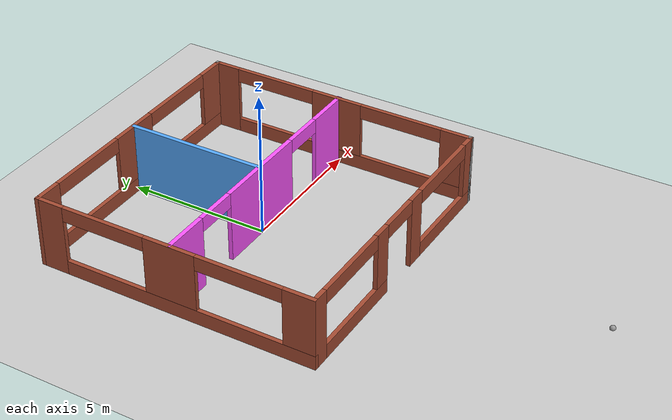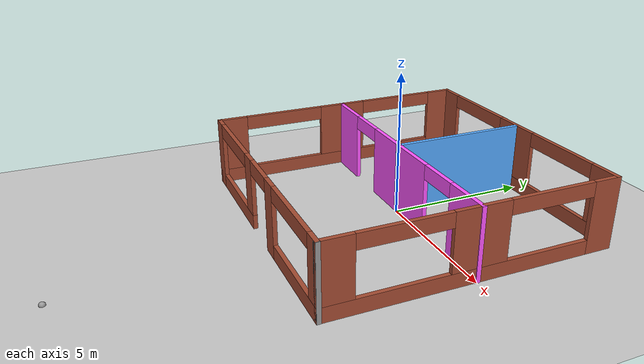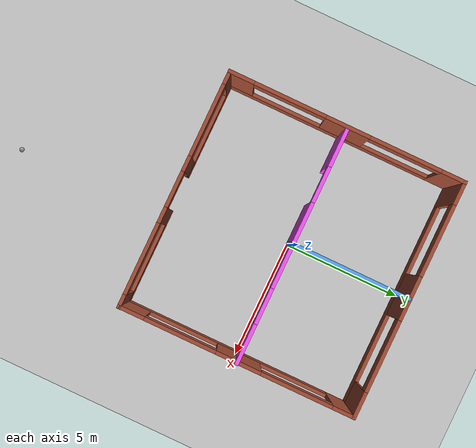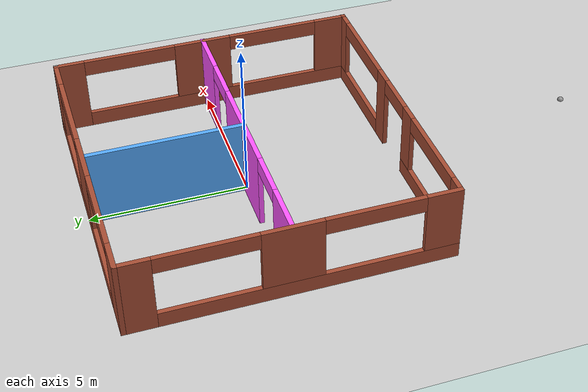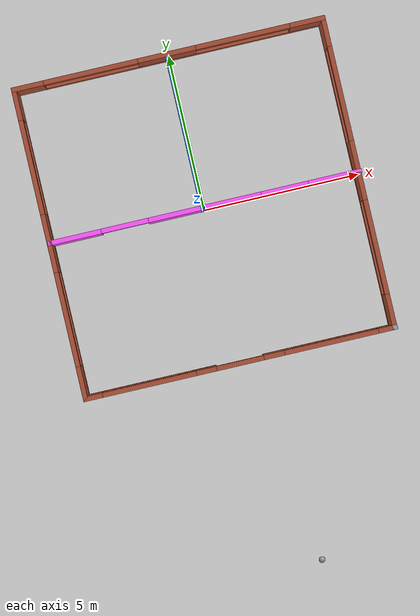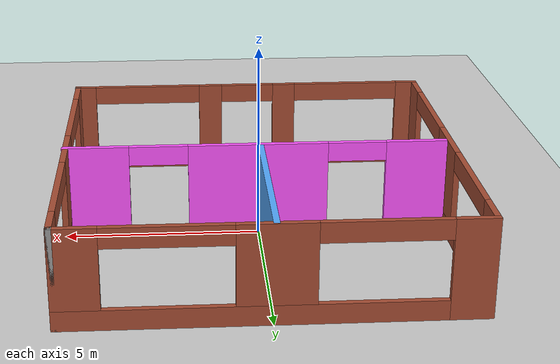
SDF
<?xml version="1.0" ?>

<sdf version="1.4">

  <world name="default">

    <include>
      <uri>model://ground_plane</uri>
    </include>

    <!-- Light source -->
    <include>
      <uri>model://sun</uri>
    </include>

    <!-- World camera -->
    <gui fullscreen='0'>
      <camera name='world_camera'>
        <pose>4.927360 -4.376610 3.740080 0.000000 0.275643 2.356190</pose>
        <view_controller>orbit</view_controller>
      </camera>
    </gui>

    <include>
      <uri>model://building</uri>
    </include>

    <model name='my_ball'>
      <link name='link_0'>
        <pose frame=''>0.04186 -0.131522 0 0 -0 0</pose>
        <inertial>
          <mass>1</mass>
          <inertia>
            <ixx>0.1</ixx>
            <ixy>0</ixy>
            <ixz>0</ixz>
            <iyy>0.1</iyy>
            <iyz>0</iyz>
            <izz>0.1</izz>
          </inertia>
          <pose frame=''>0 0 0 0 -0 0</pose>
        </inertial>
        <gravity>1</gravity>
        <self_collide>0</self_collide>
        <kinematic>0</kinematic>
        <visual name='visual'>
          <pose frame=''>0 0 0 0 -0 0</pose>
          <geometry>
            <sphere>
              <radius>0.1</radius>
            </sphere>
          </geometry>
          <material>
            <lighting>1</lighting>
            <script>
              <uri>file://media/materials/scripts/gazebo.material</uri>
              <name>Gazebo/Grey</name>
            </script>
            <shader type='pixel'>
              <normal_map>__default__</normal_map>
            </shader>
            <ambient>1 1 1 1</ambient>
            <diffuse>1 1 1 1</diffuse>
            <specular>1 1 1 1</specular>
            <emissive>1 1 1 1</emissive>
          </material>
          <transparency>0</transparency>
          <cast_shadows>1</cast_shadows>
        </visual>
        <collision name='collision'>
          <laser_retro>0</laser_retro>
          <max_contacts>10</max_contacts>
          <pose frame=''>0 0 0 0 -0 0</pose>
          <geometry>
            <sphere>
              <radius>0.1</radius>
            </sphere>
          </geometry>
          <surface>
            <friction>
              <ode>
                <mu>1</mu>
                <mu2>1</mu2>
                <fdir1>0 0 0</fdir1>
                <slip1>0</slip1>
                <slip2>0</slip2>
              </ode>
              <torsional>
                <coefficient>1</coefficient>
                <patch_radius>0</patch_radius>
                <surface_radius>0</surface_radius>
                <use_patch_radius>1</use_patch_radius>
                <ode>
                  <slip>0</slip>
                </ode>
              </torsional>
            </friction>
            <bounce>
              <restitution_coefficient>0</restitution_coefficient>
              <threshold>1e+06</threshold>
            </bounce>
            <contact>
              <collide_without_contact>0</collide_without_contact>
              <collide_without_contact_bitmask>1</collide_without_contact_bitmask>
              <collide_bitmask>1</collide_bitmask>
              <ode>
                <soft_cfm>0</soft_cfm>
                <soft_erp>0.2</soft_erp>
                <kp>1e+13</kp>
                <kd>1</kd>
                <max_vel>0.01</max_vel>
                <min_depth>0</min_depth>
              </ode>
              <bullet>
                <split_impulse>1</split_impulse>
                <split_impulse_penetration_threshold>-0.01</split_impulse_penetration_threshold>
                <soft_cfm>0</soft_cfm>
                <soft_erp>0.2</soft_erp>
                <kp>1e+13</kp>
                <kd>1</kd>
              </bullet>
            </contact>
          </surface>
        </collision>
      </link>
      <static>0</static>
      <allow_auto_disable>1</allow_auto_disable>
      <pose frame=''>1.07753 -11.4855 0 0 -0 0</pose>
    </model>

  </world>
</sdf>

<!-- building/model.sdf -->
<sdf version='1.6'>
  <model name='building'>
    <link name='Wall_0'>
      <pose frame=''>-4.938 0 0 0 0 -1.5708</pose>
      <self_collide>0</self_collide>
      <kinematic>0</kinematic>
      <visual name='Wall_0_Visual_5'>
        <pose frame=''>2.39262 0 2.25 0 -0 0</pose>
        <geometry>
          <box>
            <size>3 0.15 0.5</size>
          </box>
        </geometry>
        <material>
          <script>
            <uri>file://media/materials/scripts/gazebo.material</uri>
            <name>Gazebo/Bricks</name>
          </script>
          <ambient>1 1 1 1</ambient>
          <shader type='pixel'/>
          <diffuse>1 1 1 1</diffuse>
          <specular>0.2 0.2 0.2 1</specular>
          <emissive>0 0 0 1</emissive>
        </material>
        <meta>
          <layer>0</layer>
        </meta>
        <transparency>0</transparency>
        <cast_shadows>1</cast_shadows>
      </visual>
      <visual name='Wall_0_Visual_4'>
        <pose frame=''>-2.45121 0 2.25 0 -0 0</pose>
        <geometry>
          <box>
            <size>3 0.15 0.5</size>
          </box>
        </geometry>
        <material>
          <script>
            <uri>file://media/materials/scripts/gazebo.material</uri>
            <name>Gazebo/Bricks</name>
          </script>
          <ambient>1 1 1 1</ambient>
          <shader type='pixel'/>
          <diffuse>1 1 1 1</diffuse>
          <specular>0.2 0.2 0.2 1</specular>
          <emissive>0 0 0 1</emissive>
        </material>
        <meta>
          <layer>0</layer>
        </meta>
        <transparency>0</transparency>
        <cast_shadows>1</cast_shadows>
      </visual>
      <visual name='Wall_0_Visual_0'>
        <pose frame=''>-4.4756 0 1.25 0 -0 0</pose>
        <geometry>
          <box>
            <size>1.04879 0.15 2.5</size>
          </box>
        </geometry>
        <material>
          <script>
            <uri>file://media/materials/scripts/gazebo.material</uri>
            <name>Gazebo/Bricks</name>
          </script>
          <ambient>1 1 1 1</ambient>
          <shader type='pixel'/>
          <diffuse>1 1 1 1</diffuse>
          <specular>0.2 0.2 0.2 1</specular>
          <emissive>0 0 0 1</emissive>
        </material>
        <meta>
          <layer>0</layer>
        </meta>
        <transparency>0</transparency>
        <cast_shadows>1</cast_shadows>
      </visual>
      <visual name='Wall_0_Visual_3'>
        <pose frame=''>4.44631 0 1.5 0 -0 0</pose>
        <geometry>
          <box>
            <size>1.10737 0.15 2</size>
          </box>
        </geometry>
        <material>
          <script>
            <uri>file://media/materials/scripts/gazebo.material</uri>
            <name>Gazebo/Bricks</name>
          </script>
          <ambient>1 1 1 1</ambient>
          <shader type='pixel'/>
          <diffuse>1 1 1 1</diffuse>
          <specular>0.2 0.2 0.2 1</specular>
          <emissive>0 0 0 1</emissive>
        </material>
        <meta>
          <layer>0</layer>
        </meta>
        <transparency>0</transparency>
        <cast_shadows>1</cast_shadows>
      </visual>
      <visual name='Wall_0_Visual_2'>
        <pose frame=''>-0.029291 0 1.5 0 -0 0</pose>
        <geometry>
          <box>
            <size>1.84383 0.15 2</size>
          </box>
        </geometry>
        <material>
          <script>
            <uri>file://media/materials/scripts/gazebo.material</uri>
            <name>Gazebo/Bricks</name>
          </script>
          <ambient>1 1 1 1</ambient>
          <shader type='pixel'/>
          <diffuse>1 1 1 1</diffuse>
          <specular>0.2 0.2 0.2 1</specular>
          <emissive>0 0 0 1</emissive>
        </material>
        <meta>
          <layer>0</layer>
        </meta>
        <transparency>0</transparency>
        <cast_shadows>1</cast_shadows>
      </visual>
      <visual name='Wall_0_Visual_1'>
        <pose frame=''>0.524397 0 0.25 0 -0 0</pose>
        <geometry>
          <box>
            <size>8.95121 0.15 0.5</size>
          </box>
        </geometry>
        <material>
          <script>
            <uri>file://media/materials/scripts/gazebo.material</uri>
            <name>Gazebo/Bricks</name>
          </script>
          <ambient>1 1 1 1</ambient>
          <shader type='pixel'/>
          <diffuse>1 1 1 1</diffuse>
          <specular>0.2 0.2 0.2 1</specular>
          <emissive>0 0 0 1</emissive>
        </material>
        <meta>
          <layer>0</layer>
        </meta>
        <transparency>0</transparency>
        <cast_shadows>1</cast_shadows>
      </visual>
      <collision name='Wall_0_Collision_1'>
        <laser_retro>0</laser_retro>
        <max_contacts>10</max_contacts>
        <pose frame=''>0.524397 0 0.25 0 -0 0</pose>
        <geometry>
          <box>
            <size>8.95121 0.15 0.5</size>
          </box>
        </geometry>
        <surface>
          <friction>
            <ode>
              <mu>1</mu>
              <mu2>1</mu2>
              <fdir1>0 0 0</fdir1>
              <slip1>0</slip1>
              <slip2>0</slip2>
            </ode>
            <torsional>
              <coefficient>1</coefficient>
              <patch_radius>0</patch_radius>
              <surface_radius>0</surface_radius>
              <use_patch_radius>1</use_patch_radius>
              <ode>
                <slip>0</slip>
              </ode>
            </torsional>
          </friction>
          <bounce>
            <restitution_coefficient>0</restitution_coefficient>
            <threshold>1e+06</threshold>
          </bounce>
          <contact>
            <collide_without_contact>0</collide_without_contact>
            <collide_without_contact_bitmask>1</collide_without_contact_bitmask>
            <collide_bitmask>1</collide_bitmask>
            <ode>
              <soft_cfm>0</soft_cfm>
              <soft_erp>0.2</soft_erp>
              <kp>1e+13</kp>
              <kd>1</kd>
              <max_vel>0.01</max_vel>
              <min_depth>0</min_depth>
            </ode>
            <bullet>
              <split_impulse>1</split_impulse>
              <split_impulse_penetration_threshold>-0.01</split_impulse_penetration_threshold>
              <soft_cfm>0</soft_cfm>
              <soft_erp>0.2</soft_erp>
              <kp>1e+13</kp>
              <kd>1</kd>
            </bullet>
          </contact>
        </surface>
      </collision>
      <collision name='Wall_0_Collision_3'>
        <laser_retro>0</laser_retro>
        <max_contacts>10</max_contacts>
        <pose frame=''>4.44631 0 1.5 0 -0 0</pose>
        <geometry>
          <box>
            <size>1.10737 0.15 2</size>
          </box>
        </geometry>
        <surface>
          <friction>
            <ode>
              <mu>1</mu>
              <mu2>1</mu2>
              <fdir1>0 0 0</fdir1>
              <slip1>0</slip1>
              <slip2>0</slip2>
            </ode>
            <torsional>
              <coefficient>1</coefficient>
              <patch_radius>0</patch_radius>
              <surface_radius>0</surface_radius>
              <use_patch_radius>1</use_patch_radius>
              <ode>
                <slip>0</slip>
              </ode>
            </torsional>
          </friction>
          <bounce>
            <restitution_coefficient>0</restitution_coefficient>
            <threshold>1e+06</threshold>
          </bounce>
          <contact>
            <collide_without_contact>0</collide_without_contact>
            <collide_without_contact_bitmask>1</collide_without_contact_bitmask>
            <collide_bitmask>1</collide_bitmask>
            <ode>
              <soft_cfm>0</soft_cfm>
              <soft_erp>0.2</soft_erp>
              <kp>1e+13</kp>
              <kd>1</kd>
              <max_vel>0.01</max_vel>
              <min_depth>0</min_depth>
            </ode>
            <bullet>
              <split_impulse>1</split_impulse>
              <split_impulse_penetration_threshold>-0.01</split_impulse_penetration_threshold>
              <soft_cfm>0</soft_cfm>
              <soft_erp>0.2</soft_erp>
              <kp>1e+13</kp>
              <kd>1</kd>
            </bullet>
          </contact>
        </surface>
      </collision>
      <collision name='Wall_0_Collision_4'>
        <laser_retro>0</laser_retro>
        <max_contacts>10</max_contacts>
        <pose frame=''>-2.45121 0 2.25 0 -0 0</pose>
        <geometry>
          <box>
            <size>3 0.15 0.5</size>
          </box>
        </geometry>
        <surface>
          <friction>
            <ode>
              <mu>1</mu>
              <mu2>1</mu2>
              <fdir1>0 0 0</fdir1>
              <slip1>0</slip1>
              <slip2>0</slip2>
            </ode>
            <torsional>
              <coefficient>1</coefficient>
              <patch_radius>0</patch_radius>
              <surface_radius>0</surface_radius>
              <use_patch_radius>1</use_patch_radius>
              <ode>
                <slip>0</slip>
              </ode>
            </torsional>
          </friction>
          <bounce>
            <restitution_coefficient>0</restitution_coefficient>
            <threshold>1e+06</threshold>
          </bounce>
          <contact>
            <collide_without_contact>0</collide_without_contact>
            <collide_without_contact_bitmask>1</collide_without_contact_bitmask>
            <collide_bitmask>1</collide_bitmask>
            <ode>
              <soft_cfm>0</soft_cfm>
              <soft_erp>0.2</soft_erp>
              <kp>1e+13</kp>
              <kd>1</kd>
              <max_vel>0.01</max_vel>
              <min_depth>0</min_depth>
            </ode>
            <bullet>
              <split_impulse>1</split_impulse>
              <split_impulse_penetration_threshold>-0.01</split_impulse_penetration_threshold>
              <soft_cfm>0</soft_cfm>
              <soft_erp>0.2</soft_erp>
              <kp>1e+13</kp>
              <kd>1</kd>
            </bullet>
          </contact>
        </surface>
      </collision>
      <collision name='Wall_0_Collision_2'>
        <laser_retro>0</laser_retro>
        <max_contacts>10</max_contacts>
        <pose frame=''>-0.029291 0 1.5 0 -0 0</pose>
        <geometry>
          <box>
            <size>1.84383 0.15 2</size>
          </box>
        </geometry>
        <surface>
          <friction>
            <ode>
              <mu>1</mu>
              <mu2>1</mu2>
              <fdir1>0 0 0</fdir1>
              <slip1>0</slip1>
              <slip2>0</slip2>
            </ode>
            <torsional>
              <coefficient>1</coefficient>
              <patch_radius>0</patch_radius>
              <surface_radius>0</surface_radius>
              <use_patch_radius>1</use_patch_radius>
              <ode>
                <slip>0</slip>
              </ode>
            </torsional>
          </friction>
          <bounce>
            <restitution_coefficient>0</restitution_coefficient>
            <threshold>1e+06</threshold>
          </bounce>
          <contact>
            <collide_without_contact>0</collide_without_contact>
            <collide_without_contact_bitmask>1</collide_without_contact_bitmask>
            <collide_bitmask>1</collide_bitmask>
            <ode>
              <soft_cfm>0</soft_cfm>
              <soft_erp>0.2</soft_erp>
              <kp>1e+13</kp>
              <kd>1</kd>
              <max_vel>0.01</max_vel>
              <min_depth>0</min_depth>
            </ode>
            <bullet>
              <split_impulse>1</split_impulse>
              <split_impulse_penetration_threshold>-0.01</split_impulse_penetration_threshold>
              <soft_cfm>0</soft_cfm>
              <soft_erp>0.2</soft_erp>
              <kp>1e+13</kp>
              <kd>1</kd>
            </bullet>
          </contact>
        </surface>
      </collision>
      <collision name='Wall_0_Collision_0'>
        <laser_retro>0</laser_retro>
        <max_contacts>10</max_contacts>
        <pose frame=''>-4.4756 0 1.25 0 -0 0</pose>
        <geometry>
          <box>
            <size>1.04879 0.15 2.5</size>
          </box>
        </geometry>
        <surface>
          <friction>
            <ode>
              <mu>1</mu>
              <mu2>1</mu2>
              <fdir1>0 0 0</fdir1>
              <slip1>0</slip1>
              <slip2>0</slip2>
            </ode>
            <torsional>
              <coefficient>1</coefficient>
              <patch_radius>0</patch_radius>
              <surface_radius>0</surface_radius>
              <use_patch_radius>1</use_patch_radius>
              <ode>
                <slip>0</slip>
              </ode>
            </torsional>
          </friction>
          <bounce>
            <restitution_coefficient>0</restitution_coefficient>
            <threshold>1e+06</threshold>
          </bounce>
          <contact>
            <collide_without_contact>0</collide_without_contact>
            <collide_without_contact_bitmask>1</collide_without_contact_bitmask>
            <collide_bitmask>1</collide_bitmask>
            <ode>
              <soft_cfm>0</soft_cfm>
              <soft_erp>0.2</soft_erp>
              <kp>1e+13</kp>
              <kd>1</kd>
              <max_vel>0.01</max_vel>
              <min_depth>0</min_depth>
            </ode>
            <bullet>
              <split_impulse>1</split_impulse>
              <split_impulse_penetration_threshold>-0.01</split_impulse_penetration_threshold>
              <soft_cfm>0</soft_cfm>
              <soft_erp>0.2</soft_erp>
              <kp>1e+13</kp>
              <kd>1</kd>
            </bullet>
          </contact>
        </surface>
      </collision>
      <collision name='Wall_0_Collision_5'>
        <laser_retro>0</laser_retro>
        <max_contacts>10</max_contacts>
        <pose frame=''>2.39262 0 2.25 0 -0 0</pose>
        <geometry>
          <box>
            <size>3 0.15 0.5</size>
          </box>
        </geometry>
        <surface>
          <friction>
            <ode>
              <mu>1</mu>
              <mu2>1</mu2>
              <fdir1>0 0 0</fdir1>
              <slip1>0</slip1>
              <slip2>0</slip2>
            </ode>
            <torsional>
              <coefficient>1</coefficient>
              <patch_radius>0</patch_radius>
              <surface_radius>0</surface_radius>
              <use_patch_radius>1</use_patch_radius>
              <ode>
                <slip>0</slip>
              </ode>
            </torsional>
          </friction>
          <bounce>
            <restitution_coefficient>0</restitution_coefficient>
            <threshold>1e+06</threshold>
          </bounce>
          <contact>
            <collide_without_contact>0</collide_without_contact>
            <collide_without_contact_bitmask>1</collide_without_contact_bitmask>
            <collide_bitmask>1</collide_bitmask>
            <ode>
              <soft_cfm>0</soft_cfm>
              <soft_erp>0.2</soft_erp>
              <kp>1e+13</kp>
              <kd>1</kd>
              <max_vel>0.01</max_vel>
              <min_depth>0</min_depth>
            </ode>
            <bullet>
              <split_impulse>1</split_impulse>
              <split_impulse_penetration_threshold>-0.01</split_impulse_penetration_threshold>
              <soft_cfm>0</soft_cfm>
              <soft_erp>0.2</soft_erp>
              <kp>1e+13</kp>
              <kd>1</kd>
            </bullet>
          </contact>
        </surface>
      </collision>
    </link>
    <link name='Wall_1'>
      <pose frame=''>-0.013 -4.925 0 0 -0 0</pose>
      <self_collide>0</self_collide>
      <kinematic>0</kinematic>
      <visual name='Wall_1_Visual_0'>
        <pose frame=''>-4.69268 0 1.25 0 -0 0</pose>
        <geometry>
          <box>
            <size>0.614643 0.15 2.5</size>
          </box>
        </geometry>
        <material>
          <script>
            <uri>file://media/materials/scripts/gazebo.material</uri>
            <name>Gazebo/Bricks</name>
          </script>
          <ambient>1 1 1 1</ambient>
          <shader type='pixel'/>
          <diffuse>1 1 1 1</diffuse>
          <specular>0.2 0.2 0.2 1</specular>
          <emissive>0 0 0 1</emissive>
        </material>
        <meta>
          <layer>0</layer>
        </meta>
        <transparency>0</transparency>
        <cast_shadows>1</cast_shadows>
      </visual>
      <visual name='Wall_1_Visual_3'>
        <pose frame=''>3.2068 0 0.25 0 -0 0</pose>
        <geometry>
          <box>
            <size>3.5864 0.15 0.5</size>
          </box>
        </geometry>
        <material>
          <script>
            <uri>file://media/materials/scripts/gazebo.material</uri>
            <name>Gazebo/Bricks</name>
          </script>
          <ambient>1 1 1 1</ambient>
          <shader type='pixel'/>
          <diffuse>1 1 1 1</diffuse>
          <specular>0.2 0.2 0.2 1</specular>
          <emissive>0 0 0 1</emissive>
        </material>
        <meta>
          <layer>0</layer>
        </meta>
        <transparency>0</transparency>
        <cast_shadows>1</cast_shadows>
      </visual>
      <visual name='Wall_1_Visual_1'>
        <pose frame=''>1.08612 0 1.25 0 -0 0</pose>
        <geometry>
          <box>
            <size>0.654955 0.15 2.5</size>
          </box>
        </geometry>
        <material>
          <script>
            <uri>file://media/materials/scripts/gazebo.material</uri>
            <name>Gazebo/Bricks</name>
          </script>
          <ambient>1 1 1 1</ambient>
          <shader type='pixel'/>
          <diffuse>1 1 1 1</diffuse>
          <specular>0.2 0.2 0.2 1</specular>
          <emissive>0 0 0 1</emissive>
        </material>
        <meta>
          <layer>0</layer>
        </meta>
        <transparency>0</transparency>
        <cast_shadows>1</cast_shadows>
      </visual>
      <visual name='Wall_1_Visual_2'>
        <pose frame=''>-2.56336 0 0.25 0 -0 0</pose>
        <geometry>
          <box>
            <size>3.644 0.15 0.5</size>
          </box>
        </geometry>
        <material>
          <script>
            <uri>file://media/materials/scripts/gazebo.material</uri>
            <name>Gazebo/Bricks</name>
          </script>
          <ambient>1 1 1 1</ambient>
          <shader type='pixel'/>
          <diffuse>1 1 1 1</diffuse>
          <specular>0.2 0.2 0.2 1</specular>
          <emissive>0 0 0 1</emissive>
        </material>
        <meta>
          <layer>0</layer>
        </meta>
        <transparency>0</transparency>
        <cast_shadows>1</cast_shadows>
      </visual>
      <visual name='Wall_1_Visual_5'>
        <pose frame=''>-1.06336 0 1.5 0 -0 0</pose>
        <geometry>
          <box>
            <size>0.643998 0.15 2</size>
          </box>
        </geometry>
        <material>
          <script>
            <uri>file://media/materials/scripts/gazebo.material</uri>
            <name>Gazebo/Bricks</name>
          </script>
          <ambient>1 1 1 1</ambient>
          <shader type='pixel'/>
          <diffuse>1 1 1 1</diffuse>
          <specular>0.2 0.2 0.2 1</specular>
          <emissive>0 0 0 1</emissive>
        </material>
        <meta>
          <layer>0</layer>
        </meta>
        <transparency>0</transparency>
        <cast_shadows>1</cast_shadows>
      </visual>
      <visual name='Wall_1_Visual_6'>
        <pose frame=''>4.7068 0 1.5 0 -0 0</pose>
        <geometry>
          <box>
            <size>0.586404 0.15 2</size>
          </box>
        </geometry>
        <material>
          <script>
            <uri>file://media/materials/scripts/gazebo.material</uri>
            <name>Gazebo/Bricks</name>
          </script>
          <ambient>1 1 1 1</ambient>
          <shader type='pixel'/>
          <diffuse>1 1 1 1</diffuse>
          <specular>0.2 0.2 0.2 1</specular>
          <emissive>0 0 0 1</emissive>
        </material>
        <meta>
          <layer>0</layer>
        </meta>
        <transparency>0</transparency>
        <cast_shadows>1</cast_shadows>
      </visual>
      <visual name='Wall_1_Visual_8'>
        <pose frame=''>2.9136 0 2.25 0 -0 0</pose>
        <geometry>
          <box>
            <size>3 0.15 0.5</size>
          </box>
        </geometry>
        <material>
          <script>
            <uri>file://media/materials/scripts/gazebo.material</uri>
            <name>Gazebo/Bricks</name>
          </script>
          <ambient>1 1 1 1</ambient>
          <shader type='pixel'/>
          <diffuse>1 1 1 1</diffuse>
          <specular>0.2 0.2 0.2 1</specular>
          <emissive>0 0 0 1</emissive>
        </material>
        <meta>
          <layer>0</layer>
        </meta>
        <transparency>0</transparency>
        <cast_shadows>1</cast_shadows>
      </visual>
      <visual name='Wall_1_Visual_9'>
        <pose frame=''>0.008641 0 2.25 0 -0 0</pose>
        <geometry>
          <box>
            <size>1.5 0.15 0.5</size>
          </box>
        </geometry>
        <material>
          <script>
            <uri>file://media/materials/scripts/gazebo.material</uri>
            <name>Gazebo/Bricks</name>
          </script>
          <ambient>1 1 1 1</ambient>
          <shader type='pixel'/>
          <diffuse>1 1 1 1</diffuse>
          <specular>0.2 0.2 0.2 1</specular>
          <emissive>0 0 0 1</emissive>
        </material>
        <meta>
          <layer>0</layer>
        </meta>
        <transparency>0</transparency>
        <cast_shadows>1</cast_shadows>
      </visual>
      <visual name='Wall_1_Visual_10'>
        <pose frame=''>0.008641 0 2.25 0 -0 0</pose>
        <geometry>
          <box>
            <size>1.5 0.15 0.5</size>
          </box>
        </geometry>
        <material>
          <script>
            <uri>file://media/materials/scripts/gazebo.material</uri>
            <name>Gazebo/Bricks</name>
          </script>
          <ambient>1 1 1 1</ambient>
          <shader type='pixel'/>
          <diffuse>1 1 1 1</diffuse>
          <specular>0.2 0.2 0.2 1</specular>
          <emissive>0 0 0 1</emissive>
        </material>
        <meta>
          <layer>0</layer>
        </meta>
        <transparency>0</transparency>
        <cast_shadows>1</cast_shadows>
      </visual>
      <visual name='Wall_1_Visual_4'>
        <pose frame=''>-1.06336 0 1.5 0 -0 0</pose>
        <geometry>
          <box>
            <size>0.643998 0.15 2</size>
          </box>
        </geometry>
        <material>
          <script>
            <uri>file://media/materials/scripts/gazebo.material</uri>
            <name>Gazebo/Bricks</name>
          </script>
          <ambient>1 1 1 1</ambient>
          <shader type='pixel'/>
          <diffuse>1 1 1 1</diffuse>
          <specular>0.2 0.2 0.2 1</specular>
          <emissive>0 0 0 1</emissive>
        </material>
        <meta>
          <layer>0</layer>
        </meta>
        <transparency>0</transparency>
        <cast_shadows>1</cast_shadows>
      </visual>
      <visual name='Wall_1_Visual_7'>
        <pose frame=''>-2.88536 0 2.25 0 -0 0</pose>
        <geometry>
          <box>
            <size>3 0.15 0.5</size>
          </box>
        </geometry>
        <material>
          <script>
            <uri>file://media/materials/scripts/gazebo.material</uri>
            <name>Gazebo/Bricks</name>
          </script>
          <ambient>1 1 1 1</ambient>
          <shader type='pixel'/>
          <diffuse>1 1 1 1</diffuse>
          <specular>0.2 0.2 0.2 1</specular>
          <emissive>0 0 0 1</emissive>
        </material>
        <meta>
          <layer>0</layer>
        </meta>
        <transparency>0</transparency>
        <cast_shadows>1</cast_shadows>
      </visual>
      <collision name='Wall_1_Collision_1'>
        <laser_retro>0</laser_retro>
        <max_contacts>10</max_contacts>
        <pose frame=''>1.08612 0 1.25 0 -0 0</pose>
        <geometry>
          <box>
            <size>0.654955 0.15 2.5</size>
          </box>
        </geometry>
        <surface>
          <friction>
            <ode>
              <mu>1</mu>
              <mu2>1</mu2>
              <fdir1>0 0 0</fdir1>
              <slip1>0</slip1>
              <slip2>0</slip2>
            </ode>
            <torsional>
              <coefficient>1</coefficient>
              <patch_radius>0</patch_radius>
              <surface_radius>0</surface_radius>
              <use_patch_radius>1</use_patch_radius>
              <ode>
                <slip>0</slip>
              </ode>
            </torsional>
          </friction>
          <bounce>
            <restitution_coefficient>0</restitution_coefficient>
            <threshold>1e+06</threshold>
          </bounce>
          <contact>
            <collide_without_contact>0</collide_without_contact>
            <collide_without_contact_bitmask>1</collide_without_contact_bitmask>
            <collide_bitmask>1</collide_bitmask>
            <ode>
              <soft_cfm>0</soft_cfm>
              <soft_erp>0.2</soft_erp>
              <kp>1e+13</kp>
              <kd>1</kd>
              <max_vel>0.01</max_vel>
              <min_depth>0</min_depth>
            </ode>
            <bullet>
              <split_impulse>1</split_impulse>
              <split_impulse_penetration_threshold>-0.01</split_impulse_penetration_threshold>
              <soft_cfm>0</soft_cfm>
              <soft_erp>0.2</soft_erp>
              <kp>1e+13</kp>
              <kd>1</kd>
            </bullet>
          </contact>
        </surface>
      </collision>
      <collision name='Wall_1_Collision_9'>
        <laser_retro>0</laser_retro>
        <max_contacts>10</max_contacts>
        <pose frame=''>0.008641 0 2.25 0 -0 0</pose>
        <geometry>
          <box>
            <size>1.5 0.15 0.5</size>
          </box>
        </geometry>
        <surface>
          <friction>
            <ode>
              <mu>1</mu>
              <mu2>1</mu2>
              <fdir1>0 0 0</fdir1>
              <slip1>0</slip1>
              <slip2>0</slip2>
            </ode>
            <torsional>
              <coefficient>1</coefficient>
              <patch_radius>0</patch_radius>
              <surface_radius>0</surface_radius>
              <use_patch_radius>1</use_patch_radius>
              <ode>
                <slip>0</slip>
              </ode>
            </torsional>
          </friction>
          <bounce>
            <restitution_coefficient>0</restitution_coefficient>
            <threshold>1e+06</threshold>
          </bounce>
          <contact>
            <collide_without_contact>0</collide_without_contact>
            <collide_without_contact_bitmask>1</collide_without_contact_bitmask>
            <collide_bitmask>1</collide_bitmask>
            <ode>
              <soft_cfm>0</soft_cfm>
              <soft_erp>0.2</soft_erp>
              <kp>1e+13</kp>
              <kd>1</kd>
              <max_vel>0.01</max_vel>
              <min_depth>0</min_depth>
            </ode>
            <bullet>
              <split_impulse>1</split_impulse>
              <split_impulse_penetration_threshold>-0.01</split_impulse_penetration_threshold>
              <soft_cfm>0</soft_cfm>
              <soft_erp>0.2</soft_erp>
              <kp>1e+13</kp>
              <kd>1</kd>
            </bullet>
          </contact>
        </surface>
      </collision>
      <collision name='Wall_1_Collision_4'>
        <laser_retro>0</laser_retro>
        <max_contacts>10</max_contacts>
        <pose frame=''>-1.06336 0 1.5 0 -0 0</pose>
        <geometry>
          <box>
            <size>0.643998 0.15 2</size>
          </box>
        </geometry>
        <surface>
          <friction>
            <ode>
              <mu>1</mu>
              <mu2>1</mu2>
              <fdir1>0 0 0</fdir1>
              <slip1>0</slip1>
              <slip2>0</slip2>
            </ode>
            <torsional>
              <coefficient>1</coefficient>
              <patch_radius>0</patch_radius>
              <surface_radius>0</surface_radius>
              <use_patch_radius>1</use_patch_radius>
              <ode>
                <slip>0</slip>
              </ode>
            </torsional>
          </friction>
          <bounce>
            <restitution_coefficient>0</restitution_coefficient>
            <threshold>1e+06</threshold>
          </bounce>
          <contact>
            <collide_without_contact>0</collide_without_contact>
            <collide_without_contact_bitmask>1</collide_without_contact_bitmask>
            <collide_bitmask>1</collide_bitmask>
            <ode>
              <soft_cfm>0</soft_cfm>
              <soft_erp>0.2</soft_erp>
              <kp>1e+13</kp>
              <kd>1</kd>
              <max_vel>0.01</max_vel>
              <min_depth>0</min_depth>
            </ode>
            <bullet>
              <split_impulse>1</split_impulse>
              <split_impulse_penetration_threshold>-0.01</split_impulse_penetration_threshold>
              <soft_cfm>0</soft_cfm>
              <soft_erp>0.2</soft_erp>
              <kp>1e+13</kp>
              <kd>1</kd>
            </bullet>
          </contact>
        </surface>
      </collision>
      <collision name='Wall_1_Collision_2'>
        <laser_retro>0</laser_retro>
        <max_contacts>10</max_contacts>
        <pose frame=''>-2.56336 0 0.25 0 -0 0</pose>
        <geometry>
          <box>
            <size>3.644 0.15 0.5</size>
          </box>
        </geometry>
        <surface>
          <friction>
            <ode>
              <mu>1</mu>
              <mu2>1</mu2>
              <fdir1>0 0 0</fdir1>
              <slip1>0</slip1>
              <slip2>0</slip2>
            </ode>
            <torsional>
              <coefficient>1</coefficient>
              <patch_radius>0</patch_radius>
              <surface_radius>0</surface_radius>
              <use_patch_radius>1</use_patch_radius>
              <ode>
                <slip>0</slip>
              </ode>
            </torsional>
          </friction>
          <bounce>
            <restitution_coefficient>0</restitution_coefficient>
            <threshold>1e+06</threshold>
          </bounce>
          <contact>
            <collide_without_contact>0</collide_without_contact>
            <collide_without_contact_bitmask>1</collide_without_contact_bitmask>
            <collide_bitmask>1</collide_bitmask>
            <ode>
              <soft_cfm>0</soft_cfm>
              <soft_erp>0.2</soft_erp>
              <kp>1e+13</kp>
              <kd>1</kd>
              <max_vel>0.01</max_vel>
              <min_depth>0</min_depth>
            </ode>
            <bullet>
              <split_impulse>1</split_impulse>
              <split_impulse_penetration_threshold>-0.01</split_impulse_penetration_threshold>
              <soft_cfm>0</soft_cfm>
              <soft_erp>0.2</soft_erp>
              <kp>1e+13</kp>
              <kd>1</kd>
            </bullet>
          </contact>
        </surface>
      </collision>
      <collision name='Wall_1_Collision_8'>
        <laser_retro>0</laser_retro>
        <max_contacts>10</max_contacts>
        <pose frame=''>2.9136 0 2.25 0 -0 0</pose>
        <geometry>
          <box>
            <size>3 0.15 0.5</size>
          </box>
        </geometry>
        <surface>
          <friction>
            <ode>
              <mu>1</mu>
              <mu2>1</mu2>
              <fdir1>0 0 0</fdir1>
              <slip1>0</slip1>
              <slip2>0</slip2>
            </ode>
            <torsional>
              <coefficient>1</coefficient>
              <patch_radius>0</patch_radius>
              <surface_radius>0</surface_radius>
              <use_patch_radius>1</use_patch_radius>
              <ode>
                <slip>0</slip>
              </ode>
            </torsional>
          </friction>
          <bounce>
            <restitution_coefficient>0</restitution_coefficient>
            <threshold>1e+06</threshold>
          </bounce>
          <contact>
            <collide_without_contact>0</collide_without_contact>
            <collide_without_contact_bitmask>1</collide_without_contact_bitmask>
            <collide_bitmask>1</collide_bitmask>
            <ode>
              <soft_cfm>0</soft_cfm>
              <soft_erp>0.2</soft_erp>
              <kp>1e+13</kp>
              <kd>1</kd>
              <max_vel>0.01</max_vel>
              <min_depth>0</min_depth>
            </ode>
            <bullet>
              <split_impulse>1</split_impulse>
              <split_impulse_penetration_threshold>-0.01</split_impulse_penetration_threshold>
              <soft_cfm>0</soft_cfm>
              <soft_erp>0.2</soft_erp>
              <kp>1e+13</kp>
              <kd>1</kd>
            </bullet>
          </contact>
        </surface>
      </collision>
      <collision name='Wall_1_Collision_5'>
        <laser_retro>0</laser_retro>
        <max_contacts>10</max_contacts>
        <pose frame=''>-1.06336 0 1.5 0 -0 0</pose>
        <geometry>
          <box>
            <size>0.643998 0.15 2</size>
          </box>
        </geometry>
        <surface>
          <friction>
            <ode>
              <mu>1</mu>
              <mu2>1</mu2>
              <fdir1>0 0 0</fdir1>
              <slip1>0</slip1>
              <slip2>0</slip2>
            </ode>
            <torsional>
              <coefficient>1</coefficient>
              <patch_radius>0</patch_radius>
              <surface_radius>0</surface_radius>
              <use_patch_radius>1</use_patch_radius>
              <ode>
                <slip>0</slip>
              </ode>
            </torsional>
          </friction>
          <bounce>
            <restitution_coefficient>0</restitution_coefficient>
            <threshold>1e+06</threshold>
          </bounce>
          <contact>
            <collide_without_contact>0</collide_without_contact>
            <collide_without_contact_bitmask>1</collide_without_contact_bitmask>
            <collide_bitmask>1</collide_bitmask>
            <ode>
              <soft_cfm>0</soft_cfm>
              <soft_erp>0.2</soft_erp>
              <kp>1e+13</kp>
              <kd>1</kd>
              <max_vel>0.01</max_vel>
              <min_depth>0</min_depth>
            </ode>
            <bullet>
              <split_impulse>1</split_impulse>
              <split_impulse_penetration_threshold>-0.01</split_impulse_penetration_threshold>
              <soft_cfm>0</soft_cfm>
              <soft_erp>0.2</soft_erp>
              <kp>1e+13</kp>
              <kd>1</kd>
            </bullet>
          </contact>
        </surface>
      </collision>
      <collision name='Wall_1_Collision_3'>
        <laser_retro>0</laser_retro>
        <max_contacts>10</max_contacts>
        <pose frame=''>3.2068 0 0.25 0 -0 0</pose>
        <geometry>
          <box>
            <size>3.5864 0.15 0.5</size>
          </box>
        </geometry>
        <surface>
          <friction>
            <ode>
              <mu>1</mu>
              <mu2>1</mu2>
              <fdir1>0 0 0</fdir1>
              <slip1>0</slip1>
              <slip2>0</slip2>
            </ode>
            <torsional>
              <coefficient>1</coefficient>
              <patch_radius>0</patch_radius>
              <surface_radius>0</surface_radius>
              <use_patch_radius>1</use_patch_radius>
              <ode>
                <slip>0</slip>
              </ode>
            </torsional>
          </friction>
          <bounce>
            <restitution_coefficient>0</restitution_coefficient>
            <threshold>1e+06</threshold>
          </bounce>
          <contact>
            <collide_without_contact>0</collide_without_contact>
            <collide_without_contact_bitmask>1</collide_without_contact_bitmask>
            <collide_bitmask>1</collide_bitmask>
            <ode>
              <soft_cfm>0</soft_cfm>
              <soft_erp>0.2</soft_erp>
              <kp>1e+13</kp>
              <kd>1</kd>
              <max_vel>0.01</max_vel>
              <min_depth>0</min_depth>
            </ode>
            <bullet>
              <split_impulse>1</split_impulse>
              <split_impulse_penetration_threshold>-0.01</split_impulse_penetration_threshold>
              <soft_cfm>0</soft_cfm>
              <soft_erp>0.2</soft_erp>
              <kp>1e+13</kp>
              <kd>1</kd>
            </bullet>
          </contact>
        </surface>
      </collision>
      <collision name='Wall_1_Collision_7'>
        <laser_retro>0</laser_retro>
        <max_contacts>10</max_contacts>
        <pose frame=''>-2.88536 0 2.25 0 -0 0</pose>
        <geometry>
          <box>
            <size>3 0.15 0.5</size>
          </box>
        </geometry>
        <surface>
          <friction>
            <ode>
              <mu>1</mu>
              <mu2>1</mu2>
              <fdir1>0 0 0</fdir1>
              <slip1>0</slip1>
              <slip2>0</slip2>
            </ode>
            <torsional>
              <coefficient>1</coefficient>
              <patch_radius>0</patch_radius>
              <surface_radius>0</surface_radius>
              <use_patch_radius>1</use_patch_radius>
              <ode>
                <slip>0</slip>
              </ode>
            </torsional>
          </friction>
          <bounce>
            <restitution_coefficient>0</restitution_coefficient>
            <threshold>1e+06</threshold>
          </bounce>
          <contact>
            <collide_without_contact>0</collide_without_contact>
            <collide_without_contact_bitmask>1</collide_without_contact_bitmask>
            <collide_bitmask>1</collide_bitmask>
            <ode>
              <soft_cfm>0</soft_cfm>
              <soft_erp>0.2</soft_erp>
              <kp>1e+13</kp>
              <kd>1</kd>
              <max_vel>0.01</max_vel>
              <min_depth>0</min_depth>
            </ode>
            <bullet>
              <split_impulse>1</split_impulse>
              <split_impulse_penetration_threshold>-0.01</split_impulse_penetration_threshold>
              <soft_cfm>0</soft_cfm>
              <soft_erp>0.2</soft_erp>
              <kp>1e+13</kp>
              <kd>1</kd>
            </bullet>
          </contact>
        </surface>
      </collision>
      <collision name='Wall_1_Collision_0'>
        <laser_retro>0</laser_retro>
        <max_contacts>10</max_contacts>
        <pose frame=''>-4.69268 0 1.25 0 -0 0</pose>
        <geometry>
          <box>
            <size>0.614643 0.15 2.5</size>
          </box>
        </geometry>
        <surface>
          <friction>
            <ode>
              <mu>1</mu>
              <mu2>1</mu2>
              <fdir1>0 0 0</fdir1>
              <slip1>0</slip1>
              <slip2>0</slip2>
            </ode>
            <torsional>
              <coefficient>1</coefficient>
              <patch_radius>0</patch_radius>
              <surface_radius>0</surface_radius>
              <use_patch_radius>1</use_patch_radius>
              <ode>
                <slip>0</slip>
              </ode>
            </torsional>
          </friction>
          <bounce>
            <restitution_coefficient>0</restitution_coefficient>
            <threshold>1e+06</threshold>
          </bounce>
          <contact>
            <collide_without_contact>0</collide_without_contact>
            <collide_without_contact_bitmask>1</collide_without_contact_bitmask>
            <collide_bitmask>1</collide_bitmask>
            <ode>
              <soft_cfm>0</soft_cfm>
              <soft_erp>0.2</soft_erp>
              <kp>1e+13</kp>
              <kd>1</kd>
              <max_vel>0.01</max_vel>
              <min_depth>0</min_depth>
            </ode>
            <bullet>
              <split_impulse>1</split_impulse>
              <split_impulse_penetration_threshold>-0.01</split_impulse_penetration_threshold>
              <soft_cfm>0</soft_cfm>
              <soft_erp>0.2</soft_erp>
              <kp>1e+13</kp>
              <kd>1</kd>
            </bullet>
          </contact>
        </surface>
      </collision>
      <collision name='Wall_1_Collision_10'>
        <laser_retro>0</laser_retro>
        <max_contacts>10</max_contacts>
        <pose frame=''>0.008641 0 2.25 0 -0 0</pose>
        <geometry>
          <box>
            <size>1.5 0.15 0.5</size>
          </box>
        </geometry>
        <surface>
          <friction>
            <ode>
              <mu>1</mu>
              <mu2>1</mu2>
              <fdir1>0 0 0</fdir1>
              <slip1>0</slip1>
              <slip2>0</slip2>
            </ode>
            <torsional>
              <coefficient>1</coefficient>
              <patch_radius>0</patch_radius>
              <surface_radius>0</surface_radius>
              <use_patch_radius>1</use_patch_radius>
              <ode>
                <slip>0</slip>
              </ode>
            </torsional>
          </friction>
          <bounce>
            <restitution_coefficient>0</restitution_coefficient>
            <threshold>1e+06</threshold>
          </bounce>
          <contact>
            <collide_without_contact>0</collide_without_contact>
            <collide_without_contact_bitmask>1</collide_without_contact_bitmask>
            <collide_bitmask>1</collide_bitmask>
            <ode>
              <soft_cfm>0</soft_cfm>
              <soft_erp>0.2</soft_erp>
              <kp>1e+13</kp>
              <kd>1</kd>
              <max_vel>0.01</max_vel>
              <min_depth>0</min_depth>
            </ode>
            <bullet>
              <split_impulse>1</split_impulse>
              <split_impulse_penetration_threshold>-0.01</split_impulse_penetration_threshold>
              <soft_cfm>0</soft_cfm>
              <soft_erp>0.2</soft_erp>
              <kp>1e+13</kp>
              <kd>1</kd>
            </bullet>
          </contact>
        </surface>
      </collision>
      <collision name='Wall_1_Collision_6'>
        <laser_retro>0</laser_retro>
        <max_contacts>10</max_contacts>
        <pose frame=''>4.7068 0 1.5 0 -0 0</pose>
        <geometry>
          <box>
            <size>0.586404 0.15 2</size>
          </box>
        </geometry>
        <surface>
          <friction>
            <ode>
              <mu>1</mu>
              <mu2>1</mu2>
              <fdir1>0 0 0</fdir1>
              <slip1>0</slip1>
              <slip2>0</slip2>
            </ode>
            <torsional>
              <coefficient>1</coefficient>
              <patch_radius>0</patch_radius>
              <surface_radius>0</surface_radius>
              <use_patch_radius>1</use_patch_radius>
              <ode>
                <slip>0</slip>
              </ode>
            </torsional>
          </friction>
          <bounce>
            <restitution_coefficient>0</restitution_coefficient>
            <threshold>1e+06</threshold>
          </bounce>
          <contact>
            <collide_without_contact>0</collide_without_contact>
            <collide_without_contact_bitmask>1</collide_without_contact_bitmask>
            <collide_bitmask>1</collide_bitmask>
            <ode>
              <soft_cfm>0</soft_cfm>
              <soft_erp>0.2</soft_erp>
              <kp>1e+13</kp>
              <kd>1</kd>
              <max_vel>0.01</max_vel>
              <min_depth>0</min_depth>
            </ode>
            <bullet>
              <split_impulse>1</split_impulse>
              <split_impulse_penetration_threshold>-0.01</split_impulse_penetration_threshold>
              <soft_cfm>0</soft_cfm>
              <soft_erp>0.2</soft_erp>
              <kp>1e+13</kp>
              <kd>1</kd>
            </bullet>
          </contact>
        </surface>
      </collision>
    </link>
    <link name='Wall_14'>
      <pose frame=''>0.013 0.038 0 0 -0 0</pose>
      <self_collide>0</self_collide>
      <kinematic>0</kinematic>
      <visual name='Wall_14_Visual_0'>
        <pose frame=''>-4.14875 0 1.25 0 -0 0</pose>
        <geometry>
          <box>
            <size>1.7025 0.15 2.5</size>
          </box>
        </geometry>
        <material>
          <script>
            <uri>file://media/materials/scripts/gazebo.material</uri>
            <name>Gazebo/Grey</name>
          </script>
          <ambient>1 0.333333 1 1</ambient>
          <shader type='pixel'/>
          <diffuse>0.7 0.7 0.7 1</diffuse>
          <specular>0.01 0.01 0.01 1</specular>
          <emissive>0 0 0 1</emissive>
        </material>
        <meta>
          <layer>0</layer>
        </meta>
        <transparency>0</transparency>
        <cast_shadows>1</cast_shadows>
      </visual>
      <visual name='Wall_14_Visual_1'>
        <pose frame=''>-0.00051 0 1.25 0 -0 0</pose>
        <geometry>
          <box>
            <size>3.59398 0.15 2.5</size>
          </box>
        </geometry>
        <material>
          <script>
            <uri>file://media/materials/scripts/gazebo.material</uri>
            <name>Gazebo/Grey</name>
          </script>
          <ambient>1 0.333333 1 1</ambient>
          <shader type='pixel'/>
          <diffuse>0.7 0.7 0.7 1</diffuse>
          <specular>0.01 0.01 0.01 1</specular>
          <emissive>0 0 0 1</emissive>
        </material>
        <meta>
          <layer>0</layer>
        </meta>
        <transparency>0</transparency>
        <cast_shadows>1</cast_shadows>
      </visual>
      <visual name='Wall_14_Visual_2'>
        <pose frame=''>4.14824 0 1.25 0 -0 0</pose>
        <geometry>
          <box>
            <size>1.70352 0.15 2.5</size>
          </box>
        </geometry>
        <material>
          <script>
            <uri>file://media/materials/scripts/gazebo.material</uri>
            <name>Gazebo/Grey</name>
          </script>
          <ambient>1 0.333333 1 1</ambient>
          <shader type='pixel'/>
          <diffuse>0.7 0.7 0.7 1</diffuse>
          <specular>0.01 0.01 0.01 1</specular>
          <emissive>0 0 0 1</emissive>
        </material>
        <meta>
          <layer>0</layer>
        </meta>
        <transparency>0</transparency>
        <cast_shadows>1</cast_shadows>
      </visual>
      <visual name='Wall_14_Visual_4'>
        <pose frame=''>2.54648 0 2.25 0 -0 0</pose>
        <geometry>
          <box>
            <size>1.5 0.15 0.5</size>
          </box>
        </geometry>
        <material>
          <script>
            <uri>file://media/materials/scripts/gazebo.material</uri>
            <name>Gazebo/Grey</name>
          </script>
          <ambient>1 0.333333 1 1</ambient>
          <shader type='pixel'/>
          <diffuse>0.7 0.7 0.7 1</diffuse>
          <specular>0.01 0.01 0.01 1</specular>
          <emissive>0 0 0 1</emissive>
        </material>
        <meta>
          <layer>0</layer>
        </meta>
        <transparency>0</transparency>
        <cast_shadows>1</cast_shadows>
      </visual>
      <visual name='Wall_14_Visual_3'>
        <pose frame=''>-2.5475 0 2.25 0 -0 0</pose>
        <geometry>
          <box>
            <size>1.5 0.15 0.5</size>
          </box>
        </geometry>
        <material>
          <script>
            <uri>file://media/materials/scripts/gazebo.material</uri>
            <name>Gazebo/Grey</name>
          </script>
          <ambient>1 0.333333 1 1</ambient>
          <shader type='pixel'/>
          <diffuse>0.7 0.7 0.7 1</diffuse>
          <specular>0.01 0.01 0.01 1</specular>
          <emissive>0 0 0 1</emissive>
        </material>
        <meta>
          <layer>0</layer>
        </meta>
        <transparency>0</transparency>
        <cast_shadows>1</cast_shadows>
      </visual>
      <collision name='Wall_14_Collision_4'>
        <laser_retro>0</laser_retro>
        <max_contacts>10</max_contacts>
        <pose frame=''>2.54648 0 2.25 0 -0 0</pose>
        <geometry>
          <box>
            <size>1.5 0.15 0.5</size>
          </box>
        </geometry>
        <surface>
          <friction>
            <ode>
              <mu>1</mu>
              <mu2>1</mu2>
              <fdir1>0 0 0</fdir1>
              <slip1>0</slip1>
              <slip2>0</slip2>
            </ode>
            <torsional>
              <coefficient>1</coefficient>
              <patch_radius>0</patch_radius>
              <surface_radius>0</surface_radius>
              <use_patch_radius>1</use_patch_radius>
              <ode>
                <slip>0</slip>
              </ode>
            </torsional>
          </friction>
          <bounce>
            <restitution_coefficient>0</restitution_coefficient>
            <threshold>1e+06</threshold>
          </bounce>
          <contact>
            <collide_without_contact>0</collide_without_contact>
            <collide_without_contact_bitmask>1</collide_without_contact_bitmask>
            <collide_bitmask>1</collide_bitmask>
            <ode>
              <soft_cfm>0</soft_cfm>
              <soft_erp>0.2</soft_erp>
              <kp>1e+13</kp>
              <kd>1</kd>
              <max_vel>0.01</max_vel>
              <min_depth>0</min_depth>
            </ode>
            <bullet>
              <split_impulse>1</split_impulse>
              <split_impulse_penetration_threshold>-0.01</split_impulse_penetration_threshold>
              <soft_cfm>0</soft_cfm>
              <soft_erp>0.2</soft_erp>
              <kp>1e+13</kp>
              <kd>1</kd>
            </bullet>
          </contact>
        </surface>
      </collision>
      <collision name='Wall_14_Collision_3'>
        <laser_retro>0</laser_retro>
        <max_contacts>10</max_contacts>
        <pose frame=''>-2.5475 0 2.25 0 -0 0</pose>
        <geometry>
          <box>
            <size>1.5 0.15 0.5</size>
          </box>
        </geometry>
        <surface>
          <friction>
            <ode>
              <mu>1</mu>
              <mu2>1</mu2>
              <fdir1>0 0 0</fdir1>
              <slip1>0</slip1>
              <slip2>0</slip2>
            </ode>
            <torsional>
              <coefficient>1</coefficient>
              <patch_radius>0</patch_radius>
              <surface_radius>0</surface_radius>
              <use_patch_radius>1</use_patch_radius>
              <ode>
                <slip>0</slip>
              </ode>
            </torsional>
          </friction>
          <bounce>
            <restitution_coefficient>0</restitution_coefficient>
            <threshold>1e+06</threshold>
          </bounce>
          <contact>
            <collide_without_contact>0</collide_without_contact>
            <collide_without_contact_bitmask>1</collide_without_contact_bitmask>
            <collide_bitmask>1</collide_bitmask>
            <ode>
              <soft_cfm>0</soft_cfm>
              <soft_erp>0.2</soft_erp>
              <kp>1e+13</kp>
              <kd>1</kd>
              <max_vel>0.01</max_vel>
              <min_depth>0</min_depth>
            </ode>
            <bullet>
              <split_impulse>1</split_impulse>
              <split_impulse_penetration_threshold>-0.01</split_impulse_penetration_threshold>
              <soft_cfm>0</soft_cfm>
              <soft_erp>0.2</soft_erp>
              <kp>1e+13</kp>
              <kd>1</kd>
            </bullet>
          </contact>
        </surface>
      </collision>
      <collision name='Wall_14_Collision_0'>
        <laser_retro>0</laser_retro>
        <max_contacts>10</max_contacts>
        <pose frame=''>-4.14875 0 1.25 0 -0 0</pose>
        <geometry>
          <box>
            <size>1.7025 0.15 2.5</size>
          </box>
        </geometry>
        <surface>
          <friction>
            <ode>
              <mu>1</mu>
              <mu2>1</mu2>
              <fdir1>0 0 0</fdir1>
              <slip1>0</slip1>
              <slip2>0</slip2>
            </ode>
            <torsional>
              <coefficient>1</coefficient>
              <patch_radius>0</patch_radius>
              <surface_radius>0</surface_radius>
              <use_patch_radius>1</use_patch_radius>
              <ode>
                <slip>0</slip>
              </ode>
            </torsional>
          </friction>
          <bounce>
            <restitution_coefficient>0</restitution_coefficient>
            <threshold>1e+06</threshold>
          </bounce>
          <contact>
            <collide_without_contact>0</collide_without_contact>
            <collide_without_contact_bitmask>1</collide_without_contact_bitmask>
            <collide_bitmask>1</collide_bitmask>
            <ode>
              <soft_cfm>0</soft_cfm>
              <soft_erp>0.2</soft_erp>
              <kp>1e+13</kp>
              <kd>1</kd>
              <max_vel>0.01</max_vel>
              <min_depth>0</min_depth>
            </ode>
            <bullet>
              <split_impulse>1</split_impulse>
              <split_impulse_penetration_threshold>-0.01</split_impulse_penetration_threshold>
              <soft_cfm>0</soft_cfm>
              <soft_erp>0.2</soft_erp>
              <kp>1e+13</kp>
              <kd>1</kd>
            </bullet>
          </contact>
        </surface>
      </collision>
      <collision name='Wall_14_Collision_1'>
        <laser_retro>0</laser_retro>
        <max_contacts>10</max_contacts>
        <pose frame=''>-0.00051 0 1.25 0 -0 0</pose>
        <geometry>
          <box>
            <size>3.59398 0.15 2.5</size>
          </box>
        </geometry>
        <surface>
          <friction>
            <ode>
              <mu>1</mu>
              <mu2>1</mu2>
              <fdir1>0 0 0</fdir1>
              <slip1>0</slip1>
              <slip2>0</slip2>
            </ode>
            <torsional>
              <coefficient>1</coefficient>
              <patch_radius>0</patch_radius>
              <surface_radius>0</surface_radius>
              <use_patch_radius>1</use_patch_radius>
              <ode>
                <slip>0</slip>
              </ode>
            </torsional>
          </friction>
          <bounce>
            <restitution_coefficient>0</restitution_coefficient>
            <threshold>1e+06</threshold>
          </bounce>
          <contact>
            <collide_without_contact>0</collide_without_contact>
            <collide_without_contact_bitmask>1</collide_without_contact_bitmask>
            <collide_bitmask>1</collide_bitmask>
            <ode>
              <soft_cfm>0</soft_cfm>
              <soft_erp>0.2</soft_erp>
              <kp>1e+13</kp>
              <kd>1</kd>
              <max_vel>0.01</max_vel>
              <min_depth>0</min_depth>
            </ode>
            <bullet>
              <split_impulse>1</split_impulse>
              <split_impulse_penetration_threshold>-0.01</split_impulse_penetration_threshold>
              <soft_cfm>0</soft_cfm>
              <soft_erp>0.2</soft_erp>
              <kp>1e+13</kp>
              <kd>1</kd>
            </bullet>
          </contact>
        </surface>
      </collision>
      <collision name='Wall_14_Collision_2'>
        <laser_retro>0</laser_retro>
        <max_contacts>10</max_contacts>
        <pose frame=''>4.14824 0 1.25 0 -0 0</pose>
        <geometry>
          <box>
            <size>1.70352 0.15 2.5</size>
          </box>
        </geometry>
        <surface>
          <friction>
            <ode>
              <mu>1</mu>
              <mu2>1</mu2>
              <fdir1>0 0 0</fdir1>
              <slip1>0</slip1>
              <slip2>0</slip2>
            </ode>
            <torsional>
              <coefficient>1</coefficient>
              <patch_radius>0</patch_radius>
              <surface_radius>0</surface_radius>
              <use_patch_radius>1</use_patch_radius>
              <ode>
                <slip>0</slip>
              </ode>
            </torsional>
          </friction>
          <bounce>
            <restitution_coefficient>0</restitution_coefficient>
            <threshold>1e+06</threshold>
          </bounce>
          <contact>
            <collide_without_contact>0</collide_without_contact>
            <collide_without_contact_bitmask>1</collide_without_contact_bitmask>
            <collide_bitmask>1</collide_bitmask>
            <ode>
              <soft_cfm>0</soft_cfm>
              <soft_erp>0.2</soft_erp>
              <kp>1e+13</kp>
              <kd>1</kd>
              <max_vel>0.01</max_vel>
              <min_depth>0</min_depth>
            </ode>
            <bullet>
              <split_impulse>1</split_impulse>
              <split_impulse_penetration_threshold>-0.01</split_impulse_penetration_threshold>
              <soft_cfm>0</soft_cfm>
              <soft_erp>0.2</soft_erp>
              <kp>1e+13</kp>
              <kd>1</kd>
            </bullet>
          </contact>
        </surface>
      </collision>
    </link>
    <link name='Wall_18'>
      <pose frame=''>-0.045871 2.45735 0 0 0 -1.5708</pose>
      <self_collide>0</self_collide>
      <kinematic>0</kinematic>
      <visual name='Wall_18_Visual'>
        <pose frame=''>0 0 1.25 0 -0 0</pose>
        <geometry>
          <box>
            <size>5 0.15 2.5</size>
          </box>
        </geometry>
        <material>
          <script>
            <uri>file://media/materials/scripts/gazebo.material</uri>
            <name>Gazebo/Grey</name>
          </script>
          <ambient>0.333333 0.666667 1 1</ambient>
          <shader type='pixel'/>
          <diffuse>0.7 0.7 0.7 1</diffuse>
          <specular>0.01 0.01 0.01 1</specular>
          <emissive>0 0 0 1</emissive>
        </material>
        <meta>
          <layer>0</layer>
        </meta>
        <transparency>0</transparency>
        <cast_shadows>1</cast_shadows>
      </visual>
      <collision name='Wall_18_Collision'>
        <laser_retro>0</laser_retro>
        <max_contacts>10</max_contacts>
        <pose frame=''>0 0 1.25 0 -0 0</pose>
        <geometry>
          <box>
            <size>5 0.15 2.5</size>
          </box>
        </geometry>
        <surface>
          <friction>
            <ode>
              <mu>1</mu>
              <mu2>1</mu2>
              <fdir1>0 0 0</fdir1>
              <slip1>0</slip1>
              <slip2>0</slip2>
            </ode>
            <torsional>
              <coefficient>1</coefficient>
              <patch_radius>0</patch_radius>
              <surface_radius>0</surface_radius>
              <use_patch_radius>1</use_patch_radius>
              <ode>
                <slip>0</slip>
              </ode>
            </torsional>
          </friction>
          <bounce>
            <restitution_coefficient>0</restitution_coefficient>
            <threshold>1e+06</threshold>
          </bounce>
          <contact>
            <collide_without_contact>0</collide_without_contact>
            <collide_without_contact_bitmask>1</collide_without_contact_bitmask>
            <collide_bitmask>1</collide_bitmask>
            <ode>
              <soft_cfm>0</soft_cfm>
              <soft_erp>0.2</soft_erp>
              <kp>1e+13</kp>
              <kd>1</kd>
              <max_vel>0.01</max_vel>
              <min_depth>0</min_depth>
            </ode>
            <bullet>
              <split_impulse>1</split_impulse>
              <split_impulse_penetration_threshold>-0.01</split_impulse_penetration_threshold>
              <soft_cfm>0</soft_cfm>
              <soft_erp>0.2</soft_erp>
              <kp>1e+13</kp>
              <kd>1</kd>
            </bullet>
          </contact>
        </surface>
      </collision>
    </link>
    <link name='Wall_2'>
      <pose frame=''>4.912 -4.925 0 0 -0 0</pose>
      <self_collide>0</self_collide>
      <kinematic>0</kinematic>
      <visual name='Wall_2_Visual'>
        <pose frame=''>0 0 1.25 0 -0 0</pose>
        <geometry>
          <box>
            <size>0.15 0.15 2.5</size>
          </box>
        </geometry>
        <material>
          <script>
            <uri>file://media/materials/scripts/gazebo.material</uri>
            <name>Gazebo/Grey</name>
          </script>
          <ambient>1 1 1 1</ambient>
          <shader type='pixel'/>
          <diffuse>0.7 0.7 0.7 1</diffuse>
          <specular>0.01 0.01 0.01 1</specular>
          <emissive>0 0 0 1</emissive>
        </material>
        <meta>
          <layer>0</layer>
        </meta>
        <transparency>0</transparency>
        <cast_shadows>1</cast_shadows>
      </visual>
      <collision name='Wall_2_Collision'>
        <laser_retro>0</laser_retro>
        <max_contacts>10</max_contacts>
        <pose frame=''>0 0 1.25 0 -0 0</pose>
        <geometry>
          <box>
            <size>0.15 0.15 2.5</size>
          </box>
        </geometry>
        <surface>
          <friction>
            <ode>
              <mu>1</mu>
              <mu2>1</mu2>
              <fdir1>0 0 0</fdir1>
              <slip1>0</slip1>
              <slip2>0</slip2>
            </ode>
            <torsional>
              <coefficient>1</coefficient>
              <patch_radius>0</patch_radius>
              <surface_radius>0</surface_radius>
              <use_patch_radius>1</use_patch_radius>
              <ode>
                <slip>0</slip>
              </ode>
            </torsional>
          </friction>
          <bounce>
            <restitution_coefficient>0</restitution_coefficient>
            <threshold>1e+06</threshold>
          </bounce>
          <contact>
            <collide_without_contact>0</collide_without_contact>
            <collide_without_contact_bitmask>1</collide_without_contact_bitmask>
            <collide_bitmask>1</collide_bitmask>
            <ode>
              <soft_cfm>0</soft_cfm>
              <soft_erp>0.2</soft_erp>
              <kp>1e+13</kp>
              <kd>1</kd>
              <max_vel>0.01</max_vel>
              <min_depth>0</min_depth>
            </ode>
            <bullet>
              <split_impulse>1</split_impulse>
              <split_impulse_penetration_threshold>-0.01</split_impulse_penetration_threshold>
              <soft_cfm>0</soft_cfm>
              <soft_erp>0.2</soft_erp>
              <kp>1e+13</kp>
              <kd>1</kd>
            </bullet>
          </contact>
        </surface>
      </collision>
    </link>
    <link name='Wall_4'>
      <pose frame=''>-0.013 4.925 0 0 -0 0</pose>
      <self_collide>0</self_collide>
      <kinematic>0</kinematic>
      <visual name='Wall_4_Visual_0'>
        <pose frame=''>-4.48801 0 1.25 0 -0 0</pose>
        <geometry>
          <box>
            <size>1.02398 0.15 2.5</size>
          </box>
        </geometry>
        <material>
          <script>
            <uri>file://media/materials/scripts/gazebo.material</uri>
            <name>Gazebo/Bricks</name>
          </script>
          <ambient>1 1 1 1</ambient>
          <shader type='pixel'/>
          <diffuse>1 1 1 1</diffuse>
          <specular>0.2 0.2 0.2 1</specular>
          <emissive>0 0 0 1</emissive>
        </material>
        <meta>
          <layer>0</layer>
        </meta>
        <transparency>0</transparency>
        <cast_shadows>1</cast_shadows>
      </visual>
      <visual name='Wall_4_Visual_1'>
        <pose frame=''>0.511991 0 0.25 0 -0 0</pose>
        <geometry>
          <box>
            <size>8.97602 0.15 0.5</size>
          </box>
        </geometry>
        <material>
          <script>
            <uri>file://media/materials/scripts/gazebo.material</uri>
            <name>Gazebo/Bricks</name>
          </script>
          <ambient>1 1 1 1</ambient>
          <shader type='pixel'/>
          <diffuse>1 1 1 1</diffuse>
          <specular>0.2 0.2 0.2 1</specular>
          <emissive>0 0 0 1</emissive>
        </material>
        <meta>
          <layer>0</layer>
        </meta>
        <transparency>0</transparency>
        <cast_shadows>1</cast_shadows>
      </visual>
      <visual name='Wall_4_Visual_2'>
        <pose frame=''>-0.054103 0 1.5 0 -0 0</pose>
        <geometry>
          <box>
            <size>1.84383 0.15 2</size>
          </box>
        </geometry>
        <material>
          <script>
            <uri>file://media/materials/scripts/gazebo.material</uri>
            <name>Gazebo/Bricks</name>
          </script>
          <ambient>1 1 1 1</ambient>
          <shader type='pixel'/>
          <diffuse>1 1 1 1</diffuse>
          <specular>0.2 0.2 0.2 1</specular>
          <emissive>0 0 0 1</emissive>
        </material>
        <meta>
          <layer>0</layer>
        </meta>
        <transparency>0</transparency>
        <cast_shadows>1</cast_shadows>
      </visual>
      <visual name='Wall_4_Visual_3'>
        <pose frame=''>4.43391 0 1.5 0 -0 0</pose>
        <geometry>
          <box>
            <size>1.13219 0.15 2</size>
          </box>
        </geometry>
        <material>
          <script>
            <uri>file://media/materials/scripts/gazebo.material</uri>
            <name>Gazebo/Bricks</name>
          </script>
          <ambient>1 1 1 1</ambient>
          <shader type='pixel'/>
          <diffuse>1 1 1 1</diffuse>
          <specular>0.2 0.2 0.2 1</specular>
          <emissive>0 0 0 1</emissive>
        </material>
        <meta>
          <layer>0</layer>
        </meta>
        <transparency>0</transparency>
        <cast_shadows>1</cast_shadows>
      </visual>
      <visual name='Wall_4_Visual_4'>
        <pose frame=''>-2.47602 0 2.25 0 -0 0</pose>
        <geometry>
          <box>
            <size>3 0.15 0.5</size>
          </box>
        </geometry>
        <material>
          <script>
            <uri>file://media/materials/scripts/gazebo.material</uri>
            <name>Gazebo/Bricks</name>
          </script>
          <ambient>1 1 1 1</ambient>
          <shader type='pixel'/>
          <diffuse>1 1 1 1</diffuse>
          <specular>0.2 0.2 0.2 1</specular>
          <emissive>0 0 0 1</emissive>
        </material>
        <meta>
          <layer>0</layer>
        </meta>
        <transparency>0</transparency>
        <cast_shadows>1</cast_shadows>
      </visual>
      <visual name='Wall_4_Visual_5'>
        <pose frame=''>2.36781 0 2.25 0 -0 0</pose>
        <geometry>
          <box>
            <size>3 0.15 0.5</size>
          </box>
        </geometry>
        <material>
          <script>
            <uri>file://media/materials/scripts/gazebo.material</uri>
            <name>Gazebo/Bricks</name>
          </script>
          <ambient>1 1 1 1</ambient>
          <shader type='pixel'/>
          <diffuse>1 1 1 1</diffuse>
          <specular>0.2 0.2 0.2 1</specular>
          <emissive>0 0 0 1</emissive>
        </material>
        <meta>
          <layer>0</layer>
        </meta>
        <transparency>0</transparency>
        <cast_shadows>1</cast_shadows>
      </visual>
      <collision name='Wall_4_Collision_1'>
        <laser_retro>0</laser_retro>
        <max_contacts>10</max_contacts>
        <pose frame=''>0.511991 0 0.25 0 -0 0</pose>
        <geometry>
          <box>
            <size>8.97602 0.15 0.5</size>
          </box>
        </geometry>
        <surface>
          <friction>
            <ode>
              <mu>1</mu>
              <mu2>1</mu2>
              <fdir1>0 0 0</fdir1>
              <slip1>0</slip1>
              <slip2>0</slip2>
            </ode>
            <torsional>
              <coefficient>1</coefficient>
              <patch_radius>0</patch_radius>
              <surface_radius>0</surface_radius>
              <use_patch_radius>1</use_patch_radius>
              <ode>
                <slip>0</slip>
              </ode>
            </torsional>
          </friction>
          <bounce>
            <restitution_coefficient>0</restitution_coefficient>
            <threshold>1e+06</threshold>
          </bounce>
          <contact>
            <collide_without_contact>0</collide_without_contact>
            <collide_without_contact_bitmask>1</collide_without_contact_bitmask>
            <collide_bitmask>1</collide_bitmask>
            <ode>
              <soft_cfm>0</soft_cfm>
              <soft_erp>0.2</soft_erp>
              <kp>1e+13</kp>
              <kd>1</kd>
              <max_vel>0.01</max_vel>
              <min_depth>0</min_depth>
            </ode>
            <bullet>
              <split_impulse>1</split_impulse>
              <split_impulse_penetration_threshold>-0.01</split_impulse_penetration_threshold>
              <soft_cfm>0</soft_cfm>
              <soft_erp>0.2</soft_erp>
              <kp>1e+13</kp>
              <kd>1</kd>
            </bullet>
          </contact>
        </surface>
      </collision>
      <collision name='Wall_4_Collision_2'>
        <laser_retro>0</laser_retro>
        <max_contacts>10</max_contacts>
        <pose frame=''>-0.054103 0 1.5 0 -0 0</pose>
        <geometry>
          <box>
            <size>1.84383 0.15 2</size>
          </box>
        </geometry>
        <surface>
          <friction>
            <ode>
              <mu>1</mu>
              <mu2>1</mu2>
              <fdir1>0 0 0</fdir1>
              <slip1>0</slip1>
              <slip2>0</slip2>
            </ode>
            <torsional>
              <coefficient>1</coefficient>
              <patch_radius>0</patch_radius>
              <surface_radius>0</surface_radius>
              <use_patch_radius>1</use_patch_radius>
              <ode>
                <slip>0</slip>
              </ode>
            </torsional>
          </friction>
          <bounce>
            <restitution_coefficient>0</restitution_coefficient>
            <threshold>1e+06</threshold>
          </bounce>
          <contact>
            <collide_without_contact>0</collide_without_contact>
            <collide_without_contact_bitmask>1</collide_without_contact_bitmask>
            <collide_bitmask>1</collide_bitmask>
            <ode>
              <soft_cfm>0</soft_cfm>
              <soft_erp>0.2</soft_erp>
              <kp>1e+13</kp>
              <kd>1</kd>
              <max_vel>0.01</max_vel>
              <min_depth>0</min_depth>
            </ode>
            <bullet>
              <split_impulse>1</split_impulse>
              <split_impulse_penetration_threshold>-0.01</split_impulse_penetration_threshold>
              <soft_cfm>0</soft_cfm>
              <soft_erp>0.2</soft_erp>
              <kp>1e+13</kp>
              <kd>1</kd>
            </bullet>
          </contact>
        </surface>
      </collision>
      <collision name='Wall_4_Collision_3'>
        <laser_retro>0</laser_retro>
        <max_contacts>10</max_contacts>
        <pose frame=''>4.43391 0 1.5 0 -0 0</pose>
        <geometry>
          <box>
            <size>1.13219 0.15 2</size>
          </box>
        </geometry>
        <surface>
          <friction>
            <ode>
              <mu>1</mu>
              <mu2>1</mu2>
              <fdir1>0 0 0</fdir1>
              <slip1>0</slip1>
              <slip2>0</slip2>
            </ode>
            <torsional>
              <coefficient>1</coefficient>
              <patch_radius>0</patch_radius>
              <surface_radius>0</surface_radius>
              <use_patch_radius>1</use_patch_radius>
              <ode>
                <slip>0</slip>
              </ode>
            </torsional>
          </friction>
          <bounce>
            <restitution_coefficient>0</restitution_coefficient>
            <threshold>1e+06</threshold>
          </bounce>
          <contact>
            <collide_without_contact>0</collide_without_contact>
            <collide_without_contact_bitmask>1</collide_without_contact_bitmask>
            <collide_bitmask>1</collide_bitmask>
            <ode>
              <soft_cfm>0</soft_cfm>
              <soft_erp>0.2</soft_erp>
              <kp>1e+13</kp>
              <kd>1</kd>
              <max_vel>0.01</max_vel>
              <min_depth>0</min_depth>
            </ode>
            <bullet>
              <split_impulse>1</split_impulse>
              <split_impulse_penetration_threshold>-0.01</split_impulse_penetration_threshold>
              <soft_cfm>0</soft_cfm>
              <soft_erp>0.2</soft_erp>
              <kp>1e+13</kp>
              <kd>1</kd>
            </bullet>
          </contact>
        </surface>
      </collision>
      <collision name='Wall_4_Collision_5'>
        <laser_retro>0</laser_retro>
        <max_contacts>10</max_contacts>
        <pose frame=''>2.36781 0 2.25 0 -0 0</pose>
        <geometry>
          <box>
            <size>3 0.15 0.5</size>
          </box>
        </geometry>
        <surface>
          <friction>
            <ode>
              <mu>1</mu>
              <mu2>1</mu2>
              <fdir1>0 0 0</fdir1>
              <slip1>0</slip1>
              <slip2>0</slip2>
            </ode>
            <torsional>
              <coefficient>1</coefficient>
              <patch_radius>0</patch_radius>
              <surface_radius>0</surface_radius>
              <use_patch_radius>1</use_patch_radius>
              <ode>
                <slip>0</slip>
              </ode>
            </torsional>
          </friction>
          <bounce>
            <restitution_coefficient>0</restitution_coefficient>
            <threshold>1e+06</threshold>
          </bounce>
          <contact>
            <collide_without_contact>0</collide_without_contact>
            <collide_without_contact_bitmask>1</collide_without_contact_bitmask>
            <collide_bitmask>1</collide_bitmask>
            <ode>
              <soft_cfm>0</soft_cfm>
              <soft_erp>0.2</soft_erp>
              <kp>1e+13</kp>
              <kd>1</kd>
              <max_vel>0.01</max_vel>
              <min_depth>0</min_depth>
            </ode>
            <bullet>
              <split_impulse>1</split_impulse>
              <split_impulse_penetration_threshold>-0.01</split_impulse_penetration_threshold>
              <soft_cfm>0</soft_cfm>
              <soft_erp>0.2</soft_erp>
              <kp>1e+13</kp>
              <kd>1</kd>
            </bullet>
          </contact>
        </surface>
      </collision>
      <collision name='Wall_4_Collision_4'>
        <laser_retro>0</laser_retro>
        <max_contacts>10</max_contacts>
        <pose frame=''>-2.47602 0 2.25 0 -0 0</pose>
        <geometry>
          <box>
            <size>3 0.15 0.5</size>
          </box>
        </geometry>
        <surface>
          <friction>
            <ode>
              <mu>1</mu>
              <mu2>1</mu2>
              <fdir1>0 0 0</fdir1>
              <slip1>0</slip1>
              <slip2>0</slip2>
            </ode>
            <torsional>
              <coefficient>1</coefficient>
              <patch_radius>0</patch_radius>
              <surface_radius>0</surface_radius>
              <use_patch_radius>1</use_patch_radius>
              <ode>
                <slip>0</slip>
              </ode>
            </torsional>
          </friction>
          <bounce>
            <restitution_coefficient>0</restitution_coefficient>
            <threshold>1e+06</threshold>
          </bounce>
          <contact>
            <collide_without_contact>0</collide_without_contact>
            <collide_without_contact_bitmask>1</collide_without_contact_bitmask>
            <collide_bitmask>1</collide_bitmask>
            <ode>
              <soft_cfm>0</soft_cfm>
              <soft_erp>0.2</soft_erp>
              <kp>1e+13</kp>
              <kd>1</kd>
              <max_vel>0.01</max_vel>
              <min_depth>0</min_depth>
            </ode>
            <bullet>
              <split_impulse>1</split_impulse>
              <split_impulse_penetration_threshold>-0.01</split_impulse_penetration_threshold>
              <soft_cfm>0</soft_cfm>
              <soft_erp>0.2</soft_erp>
              <kp>1e+13</kp>
              <kd>1</kd>
            </bullet>
          </contact>
        </surface>
      </collision>
      <collision name='Wall_4_Collision_0'>
        <laser_retro>0</laser_retro>
        <max_contacts>10</max_contacts>
        <pose frame=''>-4.48801 0 1.25 0 -0 0</pose>
        <geometry>
          <box>
            <size>1.02398 0.15 2.5</size>
          </box>
        </geometry>
        <surface>
          <friction>
            <ode>
              <mu>1</mu>
              <mu2>1</mu2>
              <fdir1>0 0 0</fdir1>
              <slip1>0</slip1>
              <slip2>0</slip2>
            </ode>
            <torsional>
              <coefficient>1</coefficient>
              <patch_radius>0</patch_radius>
              <surface_radius>0</surface_radius>
              <use_patch_radius>1</use_patch_radius>
              <ode>
                <slip>0</slip>
              </ode>
            </torsional>
          </friction>
          <bounce>
            <restitution_coefficient>0</restitution_coefficient>
            <threshold>1e+06</threshold>
          </bounce>
          <contact>
            <collide_without_contact>0</collide_without_contact>
            <collide_without_contact_bitmask>1</collide_without_contact_bitmask>
            <collide_bitmask>1</collide_bitmask>
            <ode>
              <soft_cfm>0</soft_cfm>
              <soft_erp>0.2</soft_erp>
              <kp>1e+13</kp>
              <kd>1</kd>
              <max_vel>0.01</max_vel>
              <min_depth>0</min_depth>
            </ode>
            <bullet>
              <split_impulse>1</split_impulse>
              <split_impulse_penetration_threshold>-0.01</split_impulse_penetration_threshold>
              <soft_cfm>0</soft_cfm>
              <soft_erp>0.2</soft_erp>
              <kp>1e+13</kp>
              <kd>1</kd>
            </bullet>
          </contact>
        </surface>
      </collision>
    </link>
    <link name='Wall_5'>
      <pose frame=''>4.912 4.925 0 0 -0 0</pose>
      <self_collide>0</self_collide>
      <kinematic>0</kinematic>
      <visual name='Wall_5_Visual'>
        <pose frame=''>0 0 1.25 0 -0 0</pose>
        <geometry>
          <box>
            <size>0.15 0.15 2.5</size>
          </box>
        </geometry>
        <material>
          <script>
            <uri>file://media/materials/scripts/gazebo.material</uri>
            <name>Gazebo/Grey</name>
          </script>
          <ambient>1 1 1 1</ambient>
          <shader type='pixel'/>
          <diffuse>0.7 0.7 0.7 1</diffuse>
          <specular>0.01 0.01 0.01 1</specular>
          <emissive>0 0 0 1</emissive>
        </material>
        <meta>
          <layer>0</layer>
        </meta>
        <transparency>0</transparency>
        <cast_shadows>1</cast_shadows>
      </visual>
      <collision name='Wall_5_Collision'>
        <laser_retro>0</laser_retro>
        <max_contacts>10</max_contacts>
        <pose frame=''>0 0 1.25 0 -0 0</pose>
        <geometry>
          <box>
            <size>0.15 0.15 2.5</size>
          </box>
        </geometry>
        <surface>
          <friction>
            <ode>
              <mu>1</mu>
              <mu2>1</mu2>
              <fdir1>0 0 0</fdir1>
              <slip1>0</slip1>
              <slip2>0</slip2>
            </ode>
            <torsional>
              <coefficient>1</coefficient>
              <patch_radius>0</patch_radius>
              <surface_radius>0</surface_radius>
              <use_patch_radius>1</use_patch_radius>
              <ode>
                <slip>0</slip>
              </ode>
            </torsional>
          </friction>
          <bounce>
            <restitution_coefficient>0</restitution_coefficient>
            <threshold>1e+06</threshold>
          </bounce>
          <contact>
            <collide_without_contact>0</collide_without_contact>
            <collide_without_contact_bitmask>1</collide_without_contact_bitmask>
            <collide_bitmask>1</collide_bitmask>
            <ode>
              <soft_cfm>0</soft_cfm>
              <soft_erp>0.2</soft_erp>
              <kp>1e+13</kp>
              <kd>1</kd>
              <max_vel>0.01</max_vel>
              <min_depth>0</min_depth>
            </ode>
            <bullet>
              <split_impulse>1</split_impulse>
              <split_impulse_penetration_threshold>-0.01</split_impulse_penetration_threshold>
              <soft_cfm>0</soft_cfm>
              <soft_erp>0.2</soft_erp>
              <kp>1e+13</kp>
              <kd>1</kd>
            </bullet>
          </contact>
        </surface>
      </collision>
    </link>
    <link name='Wall_6'>
      <pose frame=''>4.912 0 0 0 0 -1.5708</pose>
      <self_collide>0</self_collide>
      <kinematic>0</kinematic>
      <visual name='Wall_6_Visual_0'>
        <pose frame=''>-4.50971 0 1.25 0 -0 0</pose>
        <geometry>
          <box>
            <size>0.980571 0.15 2.5</size>
          </box>
        </geometry>
        <material>
          <script>
            <uri>file://media/materials/scripts/gazebo.material</uri>
            <name>Gazebo/Bricks</name>
          </script>
          <ambient>1 1 1 1</ambient>
          <shader type='pixel'/>
          <diffuse>1 1 1 1</diffuse>
          <specular>0.2 0.2 0.2 1</specular>
          <emissive>0 0 0 1</emissive>
        </material>
        <meta>
          <layer>0</layer>
        </meta>
        <transparency>0</transparency>
        <cast_shadows>1</cast_shadows>
      </visual>
      <visual name='Wall_6_Visual_2'>
        <pose frame=''>-0.074773 0 1.5 0 -0 0</pose>
        <geometry>
          <box>
            <size>1.88931 0.15 2</size>
          </box>
        </geometry>
        <material>
          <script>
            <uri>file://media/materials/scripts/gazebo.material</uri>
            <name>Gazebo/Bricks</name>
          </script>
          <ambient>1 1 1 1</ambient>
          <shader type='pixel'/>
          <diffuse>1 1 1 1</diffuse>
          <specular>0.2 0.2 0.2 1</specular>
          <emissive>0 0 0 1</emissive>
        </material>
        <meta>
          <layer>0</layer>
        </meta>
        <transparency>0</transparency>
        <cast_shadows>1</cast_shadows>
      </visual>
      <visual name='Wall_6_Visual_1'>
        <pose frame=''>0.490285 0 0.25 0 -0 0</pose>
        <geometry>
          <box>
            <size>9.01943 0.15 0.5</size>
          </box>
        </geometry>
        <material>
          <script>
            <uri>file://media/materials/scripts/gazebo.material</uri>
            <name>Gazebo/Bricks</name>
          </script>
          <ambient>1 1 1 1</ambient>
          <shader type='pixel'/>
          <diffuse>1 1 1 1</diffuse>
          <specular>0.2 0.2 0.2 1</specular>
          <emissive>0 0 0 1</emissive>
        </material>
        <meta>
          <layer>0</layer>
        </meta>
        <transparency>0</transparency>
        <cast_shadows>1</cast_shadows>
      </visual>
      <visual name='Wall_6_Visual_3'>
        <pose frame=''>4.43494 0 1.5 0 -0 0</pose>
        <geometry>
          <box>
            <size>1.13012 0.15 2</size>
          </box>
        </geometry>
        <material>
          <script>
            <uri>file://media/materials/scripts/gazebo.material</uri>
            <name>Gazebo/Bricks</name>
          </script>
          <ambient>1 1 1 1</ambient>
          <shader type='pixel'/>
          <diffuse>1 1 1 1</diffuse>
          <specular>0.2 0.2 0.2 1</specular>
          <emissive>0 0 0 1</emissive>
        </material>
        <meta>
          <layer>0</layer>
        </meta>
        <transparency>0</transparency>
        <cast_shadows>1</cast_shadows>
      </visual>
      <visual name='Wall_6_Visual_4'>
        <pose frame=''>-2.51943 0 2.25 0 -0 0</pose>
        <geometry>
          <box>
            <size>3 0.15 0.5</size>
          </box>
        </geometry>
        <material>
          <script>
            <uri>file://media/materials/scripts/gazebo.material</uri>
            <name>Gazebo/Bricks</name>
          </script>
          <ambient>1 1 1 1</ambient>
          <shader type='pixel'/>
          <diffuse>1 1 1 1</diffuse>
          <specular>0.2 0.2 0.2 1</specular>
          <emissive>0 0 0 1</emissive>
        </material>
        <meta>
          <layer>0</layer>
        </meta>
        <transparency>0</transparency>
        <cast_shadows>1</cast_shadows>
      </visual>
      <visual name='Wall_6_Visual_5'>
        <pose frame=''>2.36988 0 2.25 0 -0 0</pose>
        <geometry>
          <box>
            <size>3 0.15 0.5</size>
          </box>
        </geometry>
        <material>
          <script>
            <uri>file://media/materials/scripts/gazebo.material</uri>
            <name>Gazebo/Bricks</name>
          </script>
          <ambient>1 1 1 1</ambient>
          <shader type='pixel'/>
          <diffuse>1 1 1 1</diffuse>
          <specular>0.2 0.2 0.2 1</specular>
          <emissive>0 0 0 1</emissive>
        </material>
        <meta>
          <layer>0</layer>
        </meta>
        <transparency>0</transparency>
        <cast_shadows>1</cast_shadows>
      </visual>
      <collision name='Wall_6_Collision_0'>
        <laser_retro>0</laser_retro>
        <max_contacts>10</max_contacts>
        <pose frame=''>-4.50971 0 1.25 0 -0 0</pose>
        <geometry>
          <box>
            <size>0.980571 0.15 2.5</size>
          </box>
        </geometry>
        <surface>
          <friction>
            <ode>
              <mu>1</mu>
              <mu2>1</mu2>
              <fdir1>0 0 0</fdir1>
              <slip1>0</slip1>
              <slip2>0</slip2>
            </ode>
            <torsional>
              <coefficient>1</coefficient>
              <patch_radius>0</patch_radius>
              <surface_radius>0</surface_radius>
              <use_patch_radius>1</use_patch_radius>
              <ode>
                <slip>0</slip>
              </ode>
            </torsional>
          </friction>
          <bounce>
            <restitution_coefficient>0</restitution_coefficient>
            <threshold>1e+06</threshold>
          </bounce>
          <contact>
            <collide_without_contact>0</collide_without_contact>
            <collide_without_contact_bitmask>1</collide_without_contact_bitmask>
            <collide_bitmask>1</collide_bitmask>
            <ode>
              <soft_cfm>0</soft_cfm>
              <soft_erp>0.2</soft_erp>
              <kp>1e+13</kp>
              <kd>1</kd>
              <max_vel>0.01</max_vel>
              <min_depth>0</min_depth>
            </ode>
            <bullet>
              <split_impulse>1</split_impulse>
              <split_impulse_penetration_threshold>-0.01</split_impulse_penetration_threshold>
              <soft_cfm>0</soft_cfm>
              <soft_erp>0.2</soft_erp>
              <kp>1e+13</kp>
              <kd>1</kd>
            </bullet>
          </contact>
        </surface>
      </collision>
      <collision name='Wall_6_Collision_1'>
        <laser_retro>0</laser_retro>
        <max_contacts>10</max_contacts>
        <pose frame=''>0.490285 0 0.25 0 -0 0</pose>
        <geometry>
          <box>
            <size>9.01943 0.15 0.5</size>
          </box>
        </geometry>
        <surface>
          <friction>
            <ode>
              <mu>1</mu>
              <mu2>1</mu2>
              <fdir1>0 0 0</fdir1>
              <slip1>0</slip1>
              <slip2>0</slip2>
            </ode>
            <torsional>
              <coefficient>1</coefficient>
              <patch_radius>0</patch_radius>
              <surface_radius>0</surface_radius>
              <use_patch_radius>1</use_patch_radius>
              <ode>
                <slip>0</slip>
              </ode>
            </torsional>
          </friction>
          <bounce>
            <restitution_coefficient>0</restitution_coefficient>
            <threshold>1e+06</threshold>
          </bounce>
          <contact>
            <collide_without_contact>0</collide_without_contact>
            <collide_without_contact_bitmask>1</collide_without_contact_bitmask>
            <collide_bitmask>1</collide_bitmask>
            <ode>
              <soft_cfm>0</soft_cfm>
              <soft_erp>0.2</soft_erp>
              <kp>1e+13</kp>
              <kd>1</kd>
              <max_vel>0.01</max_vel>
              <min_depth>0</min_depth>
            </ode>
            <bullet>
              <split_impulse>1</split_impulse>
              <split_impulse_penetration_threshold>-0.01</split_impulse_penetration_threshold>
              <soft_cfm>0</soft_cfm>
              <soft_erp>0.2</soft_erp>
              <kp>1e+13</kp>
              <kd>1</kd>
            </bullet>
          </contact>
        </surface>
      </collision>
      <collision name='Wall_6_Collision_2'>
        <laser_retro>0</laser_retro>
        <max_contacts>10</max_contacts>
        <pose frame=''>-0.074773 0 1.5 0 -0 0</pose>
        <geometry>
          <box>
            <size>1.88931 0.15 2</size>
          </box>
        </geometry>
        <surface>
          <friction>
            <ode>
              <mu>1</mu>
              <mu2>1</mu2>
              <fdir1>0 0 0</fdir1>
              <slip1>0</slip1>
              <slip2>0</slip2>
            </ode>
            <torsional>
              <coefficient>1</coefficient>
              <patch_radius>0</patch_radius>
              <surface_radius>0</surface_radius>
              <use_patch_radius>1</use_patch_radius>
              <ode>
                <slip>0</slip>
              </ode>
            </torsional>
          </friction>
          <bounce>
            <restitution_coefficient>0</restitution_coefficient>
            <threshold>1e+06</threshold>
          </bounce>
          <contact>
            <collide_without_contact>0</collide_without_contact>
            <collide_without_contact_bitmask>1</collide_without_contact_bitmask>
            <collide_bitmask>1</collide_bitmask>
            <ode>
              <soft_cfm>0</soft_cfm>
              <soft_erp>0.2</soft_erp>
              <kp>1e+13</kp>
              <kd>1</kd>
              <max_vel>0.01</max_vel>
              <min_depth>0</min_depth>
            </ode>
            <bullet>
              <split_impulse>1</split_impulse>
              <split_impulse_penetration_threshold>-0.01</split_impulse_penetration_threshold>
              <soft_cfm>0</soft_cfm>
              <soft_erp>0.2</soft_erp>
              <kp>1e+13</kp>
              <kd>1</kd>
            </bullet>
          </contact>
        </surface>
      </collision>
      <collision name='Wall_6_Collision_3'>
        <laser_retro>0</laser_retro>
        <max_contacts>10</max_contacts>
        <pose frame=''>4.43494 0 1.5 0 -0 0</pose>
        <geometry>
          <box>
            <size>1.13012 0.15 2</size>
          </box>
        </geometry>
        <surface>
          <friction>
            <ode>
              <mu>1</mu>
              <mu2>1</mu2>
              <fdir1>0 0 0</fdir1>
              <slip1>0</slip1>
              <slip2>0</slip2>
            </ode>
            <torsional>
              <coefficient>1</coefficient>
              <patch_radius>0</patch_radius>
              <surface_radius>0</surface_radius>
              <use_patch_radius>1</use_patch_radius>
              <ode>
                <slip>0</slip>
              </ode>
            </torsional>
          </friction>
          <bounce>
            <restitution_coefficient>0</restitution_coefficient>
            <threshold>1e+06</threshold>
          </bounce>
          <contact>
            <collide_without_contact>0</collide_without_contact>
            <collide_without_contact_bitmask>1</collide_without_contact_bitmask>
            <collide_bitmask>1</collide_bitmask>
            <ode>
              <soft_cfm>0</soft_cfm>
              <soft_erp>0.2</soft_erp>
              <kp>1e+13</kp>
              <kd>1</kd>
              <max_vel>0.01</max_vel>
              <min_depth>0</min_depth>
            </ode>
            <bullet>
              <split_impulse>1</split_impulse>
              <split_impulse_penetration_threshold>-0.01</split_impulse_penetration_threshold>
              <soft_cfm>0</soft_cfm>
              <soft_erp>0.2</soft_erp>
              <kp>1e+13</kp>
              <kd>1</kd>
            </bullet>
          </contact>
        </surface>
      </collision>
      <collision name='Wall_6_Collision_4'>
        <laser_retro>0</laser_retro>
        <max_contacts>10</max_contacts>
        <pose frame=''>-2.51943 0 2.25 0 -0 0</pose>
        <geometry>
          <box>
            <size>3 0.15 0.5</size>
          </box>
        </geometry>
        <surface>
          <friction>
            <ode>
              <mu>1</mu>
              <mu2>1</mu2>
              <fdir1>0 0 0</fdir1>
              <slip1>0</slip1>
              <slip2>0</slip2>
            </ode>
            <torsional>
              <coefficient>1</coefficient>
              <patch_radius>0</patch_radius>
              <surface_radius>0</surface_radius>
              <use_patch_radius>1</use_patch_radius>
              <ode>
                <slip>0</slip>
              </ode>
            </torsional>
          </friction>
          <bounce>
            <restitution_coefficient>0</restitution_coefficient>
            <threshold>1e+06</threshold>
          </bounce>
          <contact>
            <collide_without_contact>0</collide_without_contact>
            <collide_without_contact_bitmask>1</collide_without_contact_bitmask>
            <collide_bitmask>1</collide_bitmask>
            <ode>
              <soft_cfm>0</soft_cfm>
              <soft_erp>0.2</soft_erp>
              <kp>1e+13</kp>
              <kd>1</kd>
              <max_vel>0.01</max_vel>
              <min_depth>0</min_depth>
            </ode>
            <bullet>
              <split_impulse>1</split_impulse>
              <split_impulse_penetration_threshold>-0.01</split_impulse_penetration_threshold>
              <soft_cfm>0</soft_cfm>
              <soft_erp>0.2</soft_erp>
              <kp>1e+13</kp>
              <kd>1</kd>
            </bullet>
          </contact>
        </surface>
      </collision>
      <collision name='Wall_6_Collision_5'>
        <laser_retro>0</laser_retro>
        <max_contacts>10</max_contacts>
        <pose frame=''>2.36988 0 2.25 0 -0 0</pose>
        <geometry>
          <box>
            <size>3 0.15 0.5</size>
          </box>
        </geometry>
        <surface>
          <friction>
            <ode>
              <mu>1</mu>
              <mu2>1</mu2>
              <fdir1>0 0 0</fdir1>
              <slip1>0</slip1>
              <slip2>0</slip2>
            </ode>
            <torsional>
              <coefficient>1</coefficient>
              <patch_radius>0</patch_radius>
              <surface_radius>0</surface_radius>
              <use_patch_radius>1</use_patch_radius>
              <ode>
                <slip>0</slip>
              </ode>
            </torsional>
          </friction>
          <bounce>
            <restitution_coefficient>0</restitution_coefficient>
            <threshold>1e+06</threshold>
          </bounce>
          <contact>
            <collide_without_contact>0</collide_without_contact>
            <collide_without_contact_bitmask>1</collide_without_contact_bitmask>
            <collide_bitmask>1</collide_bitmask>
            <ode>
              <soft_cfm>0</soft_cfm>
              <soft_erp>0.2</soft_erp>
              <kp>1e+13</kp>
              <kd>1</kd>
              <max_vel>0.01</max_vel>
              <min_depth>0</min_depth>
            </ode>
            <bullet>
              <split_impulse>1</split_impulse>
              <split_impulse_penetration_threshold>-0.01</split_impulse_penetration_threshold>
              <soft_cfm>0</soft_cfm>
              <soft_erp>0.2</soft_erp>
              <kp>1e+13</kp>
              <kd>1</kd>
            </bullet>
          </contact>
        </surface>
      </collision>
    </link>
    <link name='Wall_7'>
      <pose frame=''>4.917 -4.925 0 0 -0 0</pose>
      <self_collide>0</self_collide>
      <kinematic>0</kinematic>
      <visual name='Wall_7_Visual'>
        <pose frame=''>0 0 1.25 0 -0 0</pose>
        <geometry>
          <box>
            <size>0.16 0.15 2.5</size>
          </box>
        </geometry>
        <material>
          <script>
            <uri>file://media/materials/scripts/gazebo.material</uri>
            <name>Gazebo/Grey</name>
          </script>
          <ambient>1 1 1 1</ambient>
          <shader type='pixel'/>
          <diffuse>0.7 0.7 0.7 1</diffuse>
          <specular>0.01 0.01 0.01 1</specular>
          <emissive>0 0 0 1</emissive>
        </material>
        <meta>
          <layer>0</layer>
        </meta>
        <transparency>0</transparency>
        <cast_shadows>1</cast_shadows>
      </visual>
      <collision name='Wall_7_Collision'>
        <laser_retro>0</laser_retro>
        <max_contacts>10</max_contacts>
        <pose frame=''>0 0 1.25 0 -0 0</pose>
        <geometry>
          <box>
            <size>0.16 0.15 2.5</size>
          </box>
        </geometry>
        <surface>
          <friction>
            <ode>
              <mu>1</mu>
              <mu2>1</mu2>
              <fdir1>0 0 0</fdir1>
              <slip1>0</slip1>
              <slip2>0</slip2>
            </ode>
            <torsional>
              <coefficient>1</coefficient>
              <patch_radius>0</patch_radius>
              <surface_radius>0</surface_radius>
              <use_patch_radius>1</use_patch_radius>
              <ode>
                <slip>0</slip>
              </ode>
            </torsional>
          </friction>
          <bounce>
            <restitution_coefficient>0</restitution_coefficient>
            <threshold>1e+06</threshold>
          </bounce>
          <contact>
            <collide_without_contact>0</collide_without_contact>
            <collide_without_contact_bitmask>1</collide_without_contact_bitmask>
            <collide_bitmask>1</collide_bitmask>
            <ode>
              <soft_cfm>0</soft_cfm>
              <soft_erp>0.2</soft_erp>
              <kp>1e+13</kp>
              <kd>1</kd>
              <max_vel>0.01</max_vel>
              <min_depth>0</min_depth>
            </ode>
            <bullet>
              <split_impulse>1</split_impulse>
              <split_impulse_penetration_threshold>-0.01</split_impulse_penetration_threshold>
              <soft_cfm>0</soft_cfm>
              <soft_erp>0.2</soft_erp>
              <kp>1e+13</kp>
              <kd>1</kd>
            </bullet>
          </contact>
        </surface>
      </collision>
    </link>
    <static>1</static>
    <allow_auto_disable>1</allow_auto_disable>
  </model>
</sdf>
